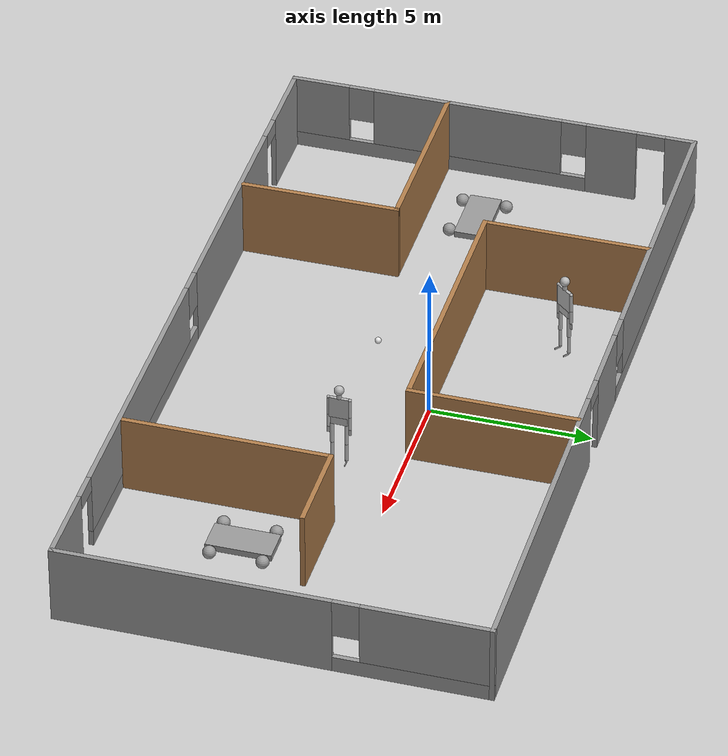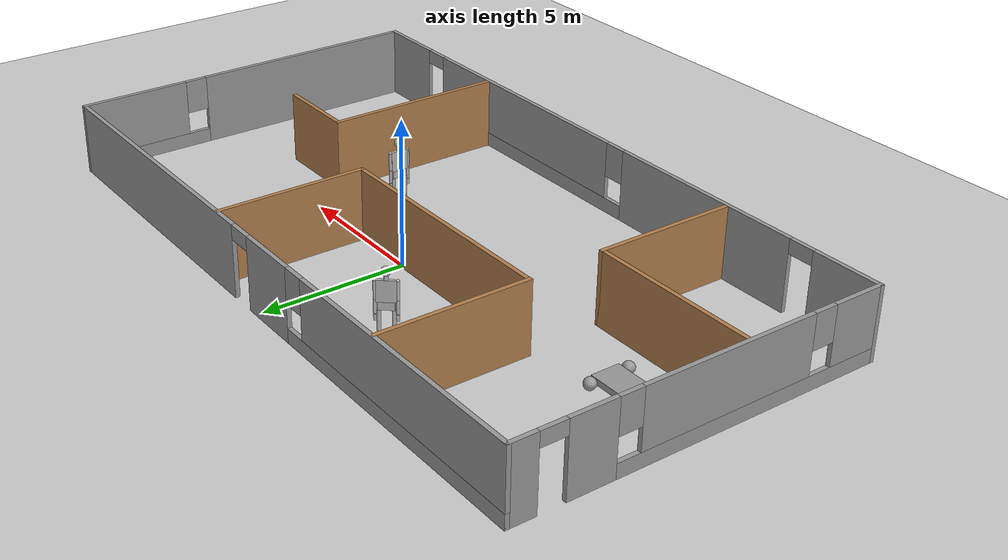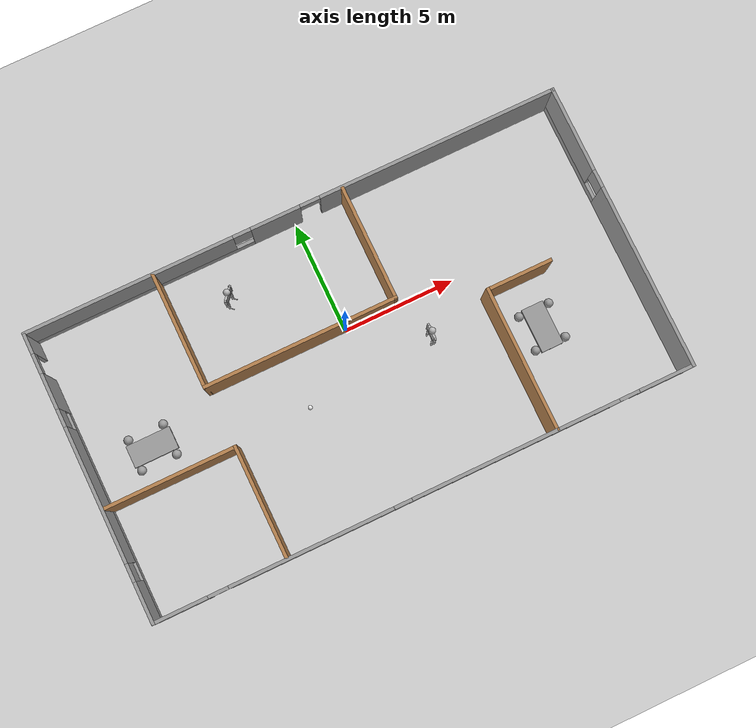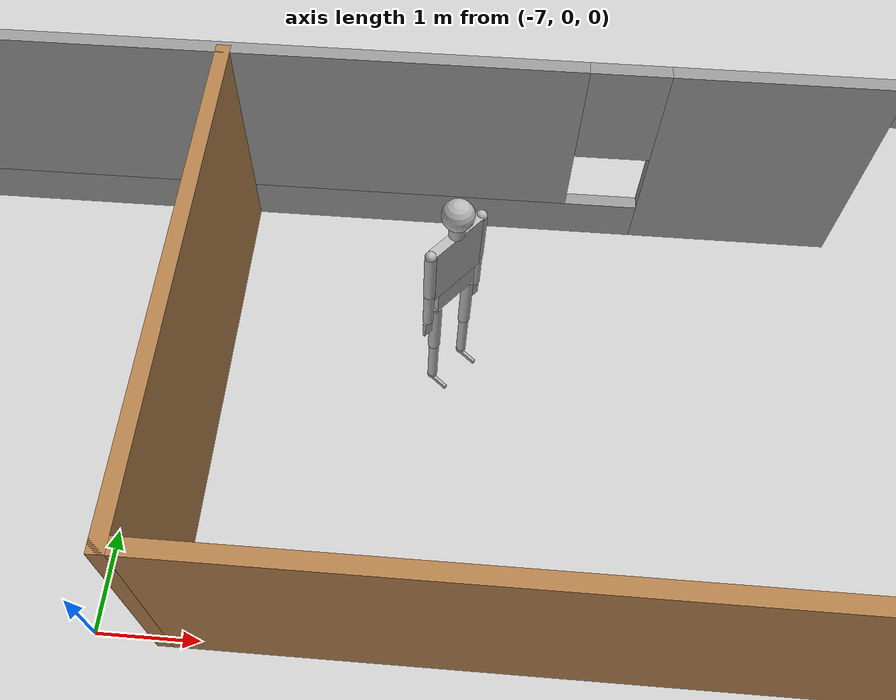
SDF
<sdf version="1.7">
 <world name="default">
  <plugin name="message" filename="libmessage.so"/>
  <light name="sun" type="directional">
   <pose>0 0 10 0 -0 0</pose>
   <diffuse>0.8 0.8 0.8 1</diffuse>
   <specular>0.2 0.2 0.2 1</specular>
   <attenuation>
    <range>1000</range>
    <constant>0.9</constant>
    <linear>0.01</linear>
    <quadratic>0.001</quadratic>
   </attenuation>
   <direction>-0.5 0.1 -0.9</direction>
   <spot><inner_angle>0</inner_angle><outer_angle>0</outer_angle><falloff>0</falloff></spot>
  </light>
  <model name="ground_plane">
   <static>1</static>
   <link name="link">
    <collision name="collision">
     <geometry><plane><normal>0 0 1</normal><size>100 100</size></plane></geometry>
     <surface>
      <contact><collide_bitmask>65535</collide_bitmask></contact>
      <friction><ode><mu>100</mu><mu2>50</mu2></ode></friction>
     </surface>
    </collision>
    <visual name="visual">
     <cast_shadows>0</cast_shadows>
     <geometry><plane><normal>0 0 1</normal><size>100 100</size></plane></geometry>
     <material>
      <script><uri>file://media/materials/scripts/gazebo.material</uri><name>Gazebo/Grey</name></script>
     </material>
    </visual>
   </link>
  </model>
  <gravity>0 0 -9.8</gravity>
  <magnetic_field>6e-06 2.3e-05 -4.2e-05</magnetic_field>
  <atmosphere type="adiabatic"/>
  <physics name="default_physics" default="0" type="ode">
   <max_step_size>0.001</max_step_size>
   <real_time_factor>1</real_time_factor>
   <real_time_update_rate>1000</real_time_update_rate>
  </physics>
  <scene><ambient>0.4 0.4 0.4 1</ambient><background>0.7 0.7 0.7 1</background><shadows>1</shadows></scene>
  <spherical_coordinates>
   <surface_model>EARTH_WGS84</surface_model>
   <latitude_deg>0</latitude_deg>
   <longitude_deg>0</longitude_deg>
   <elevation>0</elevation>
   <heading_deg>0</heading_deg>
  </spherical_coordinates>
  <model name="building">
   <pose>-0.0294 -1.27289 0 0 -0 0</pose>
   <link name="Wall_0">
    <pose>-12.05 0 0 0 0 -1.5708</pose>
    <visual name="Wall_0_Visual_0">
     <pose>-6.00515 0 1.25 0 -0 0</pose>
     <geometry><box><size>0.989706 0.15 2.5</size></box></geometry>
     <material>
      <script><uri>file://media/materials/scripts/gazebo.material</uri><name>Gazebo/Grey</name></script>
      <ambient>0.0823529 0.0823529 0.0823529 1</ambient>
     </material>
     <meta><layer>0</layer></meta>
    </visual>
    <collision name="Wall_0_Collision_0">
     <geometry><box><size>0.989706 0.15 2.5</size></box></geometry>
     <pose>-6.00515 0 1.25 0 -0 0</pose>
    </collision>
    <visual name="Wall_0_Visual_1">
     <pose>-3.80937 0 1.25 0 -0 0</pose>
     <geometry><box><size>1.60184 0.15 2.5</size></box></geometry>
     <material>
      <script><uri>file://media/materials/scripts/gazebo.material</uri><name>Gazebo/Grey</name></script>
      <ambient>0.0823529 0.0823529 0.0823529 1</ambient>
     </material>
     <meta><layer>0</layer></meta>
    </visual>
    <collision name="Wall_0_Collision_1">
     <geometry><box><size>1.60184 0.15 2.5</size></box></geometry>
     <pose>-3.80937 0 1.25 0 -0 0</pose>
    </collision>
    <visual name="Wall_0_Visual_2">
     <pose>1.74578 0 0.25 0 -0 0</pose>
     <geometry><box><size>9.50845 0.15 0.5</size></box></geometry>
     <material>
      <script><uri>file://media/materials/scripts/gazebo.material</uri><name>Gazebo/Grey</name></script>
      <ambient>0.0823529 0.0823529 0.0823529 1</ambient>
     </material>
     <meta><layer>0</layer></meta>
    </visual>
    <collision name="Wall_0_Collision_2">
     <geometry><box><size>9.50845 0.15 0.5</size></box></geometry>
     <pose>1.74578 0 0.25 0 -0 0</pose>
    </collision>
    <visual name="Wall_0_Visual_3">
     <pose>0.81488 0 1.5 0 -0 0</pose>
     <geometry><box><size>6.04666 0.15 2</size></box></geometry>
     <material>
      <script><uri>file://media/materials/scripts/gazebo.material</uri><name>Gazebo/Grey</name></script>
      <ambient>0.0823529 0.0823529 0.0823529 1</ambient>
     </material>
     <meta><layer>0</layer></meta>
    </visual>
    <collision name="Wall_0_Collision_3">
     <geometry><box><size>6.04666 0.15 2</size></box></geometry>
     <pose>0.81488 0 1.5 0 -0 0</pose>
    </collision>
    <visual name="Wall_0_Visual_4">
     <pose>5.56911 0 1.5 0 -0 0</pose>
     <geometry><box><size>1.86179 0.15 2</size></box></geometry>
     <material>
      <script><uri>file://media/materials/scripts/gazebo.material</uri><name>Gazebo/Grey</name></script>
      <ambient>0.0823529 0.0823529 0.0823529 1</ambient>
     </material>
     <meta><layer>0</layer></meta>
    </visual>
    <collision name="Wall_0_Collision_4">
     <geometry><box><size>1.86179 0.15 2</size></box></geometry>
     <pose>5.56911 0 1.5 0 -0 0</pose>
    </collision>
    <visual name="Wall_0_Visual_5">
     <pose>-2.60845 0 1.9 0 -0 0</pose>
     <geometry><box><size>0.8 0.15 1.2</size></box></geometry>
     <material>
      <script><uri>file://media/materials/scripts/gazebo.material</uri><name>Gazebo/Grey</name></script>
      <ambient>0.0823529 0.0823529 0.0823529 1</ambient>
     </material>
     <meta><layer>0</layer></meta>
    </visual>
    <collision name="Wall_0_Collision_5">
     <geometry><box><size>0.8 0.15 1.2</size></box></geometry>
     <pose>-2.60845 0 1.9 0 -0 0</pose>
    </collision>
    <visual name="Wall_0_Visual_6">
     <pose>4.23821 0 1.9 0 -0 0</pose>
     <geometry><box><size>0.8 0.15 1.2</size></box></geometry>
     <material>
      <script><uri>file://media/materials/scripts/gazebo.material</uri><name>Gazebo/Grey</name></script>
      <ambient>0.0823529 0.0823529 0.0823529 1</ambient>
     </material>
     <meta><layer>0</layer></meta>
    </visual>
    <collision name="Wall_0_Collision_6">
     <geometry><box><size>0.8 0.15 1.2</size></box></geometry>
     <pose>4.23821 0 1.9 0 -0 0</pose>
    </collision>
    <visual name="Wall_0_Visual_7">
     <pose>-5.06029 0 2.25 0 -0 0</pose>
     <geometry><box><size>0.9 0.15 0.5</size></box></geometry>
     <material>
      <script><uri>file://media/materials/scripts/gazebo.material</uri><name>Gazebo/Grey</name></script>
      <ambient>0.0823529 0.0823529 0.0823529 1</ambient>
     </material>
     <meta><layer>0</layer></meta>
    </visual>
    <collision name="Wall_0_Collision_7">
     <geometry><box><size>0.9 0.15 0.5</size></box></geometry>
     <pose>-5.06029 0 2.25 0 -0 0</pose>
    </collision>
   </link>
   <link name="Wall_1">
    <pose>0 -6.425 0 0 -0 0</pose>
    <visual name="Wall_1_Visual_0">
     <pose>-10.89 0 1.25 0 -0 0</pose>
     <geometry><box><size>2.47006 0.15 2.5</size></box></geometry>
     <material>
      <script><uri>file://media/materials/scripts/gazebo.material</uri><name>Gazebo/Grey</name></script>
      <ambient>0.0823529 0.0823529 0.0823529 1</ambient>
     </material>
     <meta><layer>0</layer></meta>
    </visual>
    <collision name="Wall_1_Collision_0">
     <geometry><box><size>2.47006 0.15 2.5</size></box></geometry>
     <pose>-10.89 0 1.25 0 -0 0</pose>
    </collision>
    <visual name="Wall_1_Visual_1">
     <pose>-5.09738 0 1.25 0 -0 0</pose>
     <geometry><box><size>7.3151 0.15 2.5</size></box></geometry>
     <material>
      <script><uri>file://media/materials/scripts/gazebo.material</uri><name>Gazebo/Grey</name></script>
      <ambient>0.0823529 0.0823529 0.0823529 1</ambient>
     </material>
     <meta><layer>0</layer></meta>
    </visual>
    <collision name="Wall_1_Collision_1">
     <geometry><box><size>7.3151 0.15 2.5</size></box></geometry>
     <pose>-5.09738 0 1.25 0 -0 0</pose>
    </collision>
    <visual name="Wall_1_Visual_2">
     <pose>10.8563 0 1.25 0 -0 0</pose>
     <geometry><box><size>2.53736 0.15 2.5</size></box></geometry>
     <material>
      <script><uri>file://media/materials/scripts/gazebo.material</uri><name>Gazebo/Grey</name></script>
      <ambient>0.0823529 0.0823529 0.0823529 1</ambient>
     </material>
     <meta><layer>0</layer></meta>
    </visual>
    <collision name="Wall_1_Collision_2">
     <geometry><box><size>2.53736 0.15 2.5</size></box></geometry>
     <pose>10.8563 0 1.25 0 -0 0</pose>
    </collision>
    <visual name="Wall_1_Visual_3">
     <pose>3.6239 0 0.25 0 -0 0</pose>
     <geometry><box><size>10.1275 0.15 0.5</size></box></geometry>
     <material>
      <script><uri>file://media/materials/scripts/gazebo.material</uri><name>Gazebo/Grey</name></script>
      <ambient>0.0823529 0.0823529 0.0823529 1</ambient>
     </material>
     <meta><layer>0</layer></meta>
    </visual>
    <collision name="Wall_1_Collision_3">
     <geometry><box><size>10.1275 0.15 0.5</size></box></geometry>
     <pose>3.6239 0 0.25 0 -0 0</pose>
    </collision>
    <visual name="Wall_1_Visual_4">
     <pose>4.0239 0 1.5 0 -0 0</pose>
     <geometry><box><size>9.32747 0.15 2</size></box></geometry>
     <material>
      <script><uri>file://media/materials/scripts/gazebo.material</uri><name>Gazebo/Grey</name></script>
      <ambient>0.0823529 0.0823529 0.0823529 1</ambient>
     </material>
     <meta><layer>0</layer></meta>
    </visual>
    <collision name="Wall_1_Collision_4">
     <geometry><box><size>9.32747 0.15 2</size></box></geometry>
     <pose>4.0239 0 1.5 0 -0 0</pose>
    </collision>
    <visual name="Wall_1_Visual_5">
     <pose>-1.03983 0 1.9 0 -0 0</pose>
     <geometry><box><size>0.8 0.15 1.2</size></box></geometry>
     <material>
      <script><uri>file://media/materials/scripts/gazebo.material</uri><name>Gazebo/Grey</name></script>
      <ambient>0.0823529 0.0823529 0.0823529 1</ambient>
     </material>
     <meta><layer>0</layer></meta>
    </visual>
    <collision name="Wall_1_Collision_5">
     <geometry><box><size>0.8 0.15 1.2</size></box></geometry>
     <pose>-1.03983 0 1.9 0 -0 0</pose>
    </collision>
    <visual name="Wall_1_Visual_6">
     <pose>-9.20494 0 2.25 0 -0 0</pose>
     <geometry><box><size>0.9 0.15 0.5</size></box></geometry>
     <material>
      <script><uri>file://media/materials/scripts/gazebo.material</uri><name>Gazebo/Grey</name></script>
      <ambient>0.0823529 0.0823529 0.0823529 1</ambient>
     </material>
     <meta><layer>0</layer></meta>
    </visual>
    <collision name="Wall_1_Collision_6">
     <geometry><box><size>0.9 0.15 0.5</size></box></geometry>
     <pose>-9.20494 0 2.25 0 -0 0</pose>
    </collision>
    <visual name="Wall_1_Visual_7">
     <pose>9.13764 0 2.25 0 -0 0</pose>
     <geometry><box><size>0.9 0.15 0.5</size></box></geometry>
     <material>
      <script><uri>file://media/materials/scripts/gazebo.material</uri><name>Gazebo/Grey</name></script>
      <ambient>0.0823529 0.0823529 0.0823529 1</ambient>
     </material>
     <meta><layer>0</layer></meta>
    </visual>
    <collision name="Wall_1_Collision_7">
     <geometry><box><size>0.9 0.15 0.5</size></box></geometry>
     <pose>9.13764 0 2.25 0 -0 0</pose>
    </collision>
   </link>
   <link name="Wall_10">
    <collision name="Wall_10_Collision">
     <geometry><box><size>3 0.15 2.5</size></box></geometry>
     <pose>0 0 1.25 0 -0 0</pose>
    </collision>
    <visual name="Wall_10_Visual">
     <pose>0 0 1.25 0 -0 0</pose>
     <geometry><box><size>3 0.15 2.5</size></box></geometry>
     <material>
      <script><uri>file://media/materials/scripts/gazebo.material</uri><name>Gazebo/Wood</name></script>
      <ambient>1 1 1 1</ambient>
     </material>
     <meta><layer>0</layer></meta>
    </visual>
    <pose>7.30122 -0.039357 0 0 -0 0</pose>
   </link>
   <link name="Wall_12">
    <collision name="Wall_12_Collision">
     <geometry><box><size>6 0.15 2.5</size></box></geometry>
     <pose>0 0 1.25 0 -0 0</pose>
    </collision>
    <visual name="Wall_12_Visual">
     <pose>0 0 1.25 0 -0 0</pose>
     <geometry><box><size>6 0.15 2.5</size></box></geometry>
     <material>
      <script><uri>file://media/materials/scripts/gazebo.material</uri><name>Gazebo/Wood</name></script>
      <ambient>1 1 1 1</ambient>
     </material>
     <meta><layer>0</layer></meta>
    </visual>
    <pose>-9.10187 -1.46254 0 0 -0 0</pose>
   </link>
   <link name="Wall_13">
    <collision name="Wall_13_Collision">
     <geometry><box><size>5 0.15 2.5</size></box></geometry>
     <pose>0 0 1.25 0 -0 0</pose>
    </collision>
    <visual name="Wall_13_Visual">
     <pose>0 0 1.25 0 -0 0</pose>
     <geometry><box><size>5 0.15 2.5</size></box></geometry>
     <material>
      <script><uri>file://media/materials/scripts/gazebo.material</uri><name>Gazebo/Wood</name></script>
      <ambient>1 1 1 1</ambient>
     </material>
     <meta><layer>0</layer></meta>
    </visual>
    <pose>-6.17687 -3.88754 0 0 0 -1.5708</pose>
   </link>
   <link name="Wall_2">
    <pose>12.05 0 0 0 -0 1.5708</pose>
    <visual name="Wall_2_Visual_0">
     <pose>-2.35395 0 1.25 0 -0 0</pose>
     <geometry><box><size>8.2921 0.15 2.5</size></box></geometry>
     <material>
      <script><uri>file://media/materials/scripts/gazebo.material</uri><name>Gazebo/Grey</name></script>
      <ambient>0.0823529 0.0823529 0.0823529 1</ambient>
     </material>
     <meta><layer>0</layer></meta>
    </visual>
    <collision name="Wall_2_Collision_0">
     <geometry><box><size>8.2921 0.15 2.5</size></box></geometry>
     <pose>-2.35395 0 1.25 0 -0 0</pose>
    </collision>
    <visual name="Wall_2_Visual_1">
     <pose>4.14605 0 0.25 0 -0 0</pose>
     <geometry><box><size>4.7079 0.15 0.5</size></box></geometry>
     <material>
      <script><uri>file://media/materials/scripts/gazebo.material</uri><name>Gazebo/Grey</name></script>
      <ambient>0.0823529 0.0823529 0.0823529 1</ambient>
     </material>
     <meta><layer>0</layer></meta>
    </visual>
    <collision name="Wall_2_Collision_1">
     <geometry><box><size>4.7079 0.15 0.5</size></box></geometry>
     <pose>4.14605 0 0.25 0 -0 0</pose>
    </collision>
    <visual name="Wall_2_Visual_2">
     <pose>4.54605 0 1.5 0 -0 0</pose>
     <geometry><box><size>3.9079 0.15 2</size></box></geometry>
     <material>
      <script><uri>file://media/materials/scripts/gazebo.material</uri><name>Gazebo/Grey</name></script>
      <ambient>0.0823529 0.0823529 0.0823529 1</ambient>
     </material>
     <meta><layer>0</layer></meta>
    </visual>
    <collision name="Wall_2_Collision_2">
     <geometry><box><size>3.9079 0.15 2</size></box></geometry>
     <pose>4.54605 0 1.5 0 -0 0</pose>
    </collision>
    <visual name="Wall_2_Visual_3">
     <pose>2.1921 0 1.9 0 -0 0</pose>
     <geometry><box><size>0.8 0.15 1.2</size></box></geometry>
     <material>
      <script><uri>file://media/materials/scripts/gazebo.material</uri><name>Gazebo/Grey</name></script>
      <ambient>0.0823529 0.0823529 0.0823529 1</ambient>
     </material>
     <meta><layer>0</layer></meta>
    </visual>
    <collision name="Wall_2_Collision_3">
     <geometry><box><size>0.8 0.15 1.2</size></box></geometry>
     <pose>2.1921 0 1.9 0 -0 0</pose>
    </collision>
   </link>
   <link name="Wall_3">
    <pose>0 6.425 0 0 -0 3.14159</pose>
    <visual name="Wall_3_Visual_0">
     <pose>-6.70437 0 1.25 0 -0 0</pose>
     <geometry><box><size>10.8413 0.15 2.5</size></box></geometry>
     <material>
      <script><uri>file://media/materials/scripts/gazebo.material</uri><name>Gazebo/Grey</name></script>
      <ambient>0.0823529 0.0823529 0.0823529 1</ambient>
     </material>
     <meta><layer>0</layer></meta>
    </visual>
    <collision name="Wall_3_Collision_0">
     <geometry><box><size>10.8413 0.15 2.5</size></box></geometry>
     <pose>-6.70437 0 1.25 0 -0 0</pose>
    </collision>
    <visual name="Wall_3_Visual_1">
     <pose>0.741002 0 1.25 0 -0 0</pose>
     <geometry><box><size>2.2495 0.15 2.5</size></box></geometry>
     <material>
      <script><uri>file://media/materials/scripts/gazebo.material</uri><name>Gazebo/Grey</name></script>
      <ambient>0.0823529 0.0823529 0.0823529 1</ambient>
     </material>
     <meta><layer>0</layer></meta>
    </visual>
    <collision name="Wall_3_Collision_1">
     <geometry><box><size>2.2495 0.15 2.5</size></box></geometry>
     <pose>0.741002 0 1.25 0 -0 0</pose>
    </collision>
    <visual name="Wall_3_Visual_2">
     <pose>6.99538 0 0.25 0 -0 0</pose>
     <geometry><box><size>10.2592 0.15 0.5</size></box></geometry>
     <material>
      <script><uri>file://media/materials/scripts/gazebo.material</uri><name>Gazebo/Grey</name></script>
      <ambient>0.0823529 0.0823529 0.0823529 1</ambient>
     </material>
     <meta><layer>0</layer></meta>
    </visual>
    <collision name="Wall_3_Collision_2">
     <geometry><box><size>10.2592 0.15 0.5</size></box></geometry>
     <pose>6.99538 0 0.25 0 -0 0</pose>
    </collision>
    <visual name="Wall_3_Visual_3">
     <pose>7.39538 0 1.5 0 -0 0</pose>
     <geometry><box><size>9.45925 0.15 2</size></box></geometry>
     <material>
      <script><uri>file://media/materials/scripts/gazebo.material</uri><name>Gazebo/Grey</name></script>
      <ambient>0.0823529 0.0823529 0.0823529 1</ambient>
     </material>
     <meta><layer>0</layer></meta>
    </visual>
    <collision name="Wall_3_Collision_3">
     <geometry><box><size>9.45925 0.15 2</size></box></geometry>
     <pose>7.39538 0 1.5 0 -0 0</pose>
    </collision>
    <visual name="Wall_3_Visual_4">
     <pose>2.26575 0 1.9 0 -0 0</pose>
     <geometry><box><size>0.8 0.15 1.2</size></box></geometry>
     <material>
      <script><uri>file://media/materials/scripts/gazebo.material</uri><name>Gazebo/Grey</name></script>
      <ambient>0.0823529 0.0823529 0.0823529 1</ambient>
     </material>
     <meta><layer>0</layer></meta>
    </visual>
    <collision name="Wall_3_Collision_4">
     <geometry><box><size>0.8 0.15 1.2</size></box></geometry>
     <pose>2.26575 0 1.9 0 -0 0</pose>
    </collision>
    <visual name="Wall_3_Visual_5">
     <pose>-0.833748 0 2.25 0 -0 0</pose>
     <geometry><box><size>0.9 0.15 0.5</size></box></geometry>
     <material>
      <script><uri>file://media/materials/scripts/gazebo.material</uri><name>Gazebo/Grey</name></script>
      <ambient>0.0823529 0.0823529 0.0823529 1</ambient>
     </material>
     <meta><layer>0</layer></meta>
    </visual>
    <collision name="Wall_3_Collision_5">
     <geometry><box><size>0.9 0.15 0.5</size></box></geometry>
     <pose>-0.833748 0 2.25 0 -0 0</pose>
    </collision>
   </link>
   <link name="Wall_5">
    <collision name="Wall_5_Collision">
     <geometry><box><size>5.25 0.15 2.5</size></box></geometry>
     <pose>0 0 1.25 0 -0 0</pose>
    </collision>
    <visual name="Wall_5_Visual">
     <pose>0 0 1.25 0 -0 0</pose>
     <geometry><box><size>5.25 0.15 2.5</size></box></geometry>
     <material>
      <script><uri>file://media/materials/scripts/gazebo.material</uri><name>Gazebo/Wood</name></script>
      <ambient>1 1 1 1</ambient>
     </material>
     <meta><layer>0</layer></meta>
    </visual>
    <pose>-6.29048 3.82874 0 0 0 -1.5708</pose>
   </link>
   <link name="Wall_6">
    <collision name="Wall_6_Collision">
     <geometry><box><size>8.75 0.15 2.5</size></box></geometry>
     <pose>0 0 1.25 0 -0 0</pose>
    </collision>
    <visual name="Wall_6_Visual">
     <pose>0 0 1.25 0 -0 0</pose>
     <geometry><box><size>8.75 0.15 2.5</size></box></geometry>
     <material>
      <script><uri>file://media/materials/scripts/gazebo.material</uri><name>Gazebo/Wood</name></script>
      <ambient>1 1 1 1</ambient>
     </material>
     <meta><layer>0</layer></meta>
    </visual>
    <pose>-1.99048 1.27874 0 0 -0 0</pose>
   </link>
   <link name="Wall_7">
    <collision name="Wall_7_Collision">
     <geometry><box><size>5.25 0.15 2.5</size></box></geometry>
     <pose>0 0 1.25 0 -0 0</pose>
    </collision>
    <visual name="Wall_7_Visual">
     <pose>0 0 1.25 0 -0 0</pose>
     <geometry><box><size>5.25 0.15 2.5</size></box></geometry>
     <material>
      <script><uri>file://media/materials/scripts/gazebo.material</uri><name>Gazebo/Wood</name></script>
      <ambient>1 1 1 1</ambient>
     </material>
     <meta><layer>0</layer></meta>
    </visual>
    <pose>2.30952 3.82874 0 0 -0 1.5708</pose>
   </link>
   <link name="Wall_9">
    <collision name="Wall_9_Collision">
     <geometry><box><size>6.5 0.15 2.5</size></box></geometry>
     <pose>0 0 1.25 0 -0 0</pose>
    </collision>
    <visual name="Wall_9_Visual">
     <pose>0 0 1.25 0 -0 0</pose>
     <geometry><box><size>6.5 0.15 2.5</size></box></geometry>
     <material>
      <script><uri>file://media/materials/scripts/gazebo.material</uri><name>Gazebo/Wood</name></script>
      <ambient>1 1 1 1</ambient>
     </material>
     <meta><layer>0</layer></meta>
    </visual>
    <pose>5.87622 -3.21436 0 0 -0 1.5708</pose>
   </link>
   <static>1</static>
  </model>
  <model name="object">
   <link name="link_0">
    <pose>-2.35749 -2.62116 0.5 0 -0 0</pose>
    <inertial>
     <mass>1</mass>
     <inertia>
      <ixx>0.166667</ixx>
      <ixy>0</ixy>
      <ixz>0</ixz>
      <iyy>0.166667</iyy>
      <iyz>0</iyz>
      <izz>0.166667</izz>
     </inertia>
    </inertial>
    <visual name="visual">
     <geometry><box><size>2 1 0.2</size></box></geometry>
     <material>
      <lighting>1</lighting>
      <script><uri>file://media/materials/scripts/gazebo.material</uri><name>Gazebo/Grey</name></script>
      <shader type="pixel"><normal_map>__default__</normal_map></shader>
      <ambient>0.3 0.3 0.3 1</ambient>
      <diffuse>0.7 0.7 0.7 1</diffuse>
      <specular>0.01 0.01 0.01 1</specular>
      <emissive>0 0 0 1</emissive>
     </material>
    </visual>
    <collision name="collision">
     <geometry><box><size>2 1 0.2</size></box></geometry>
     <surface>
      <friction>
       <ode><mu>1</mu><mu2>1</mu2><fdir1>0 0 0</fdir1><slip1>0</slip1><slip2>0</slip2></ode>
       <torsional>
        <coefficient>1</coefficient>
        <patch_radius>0</patch_radius>
        <surface_radius>0</surface_radius>
        <use_patch_radius>1</use_patch_radius>
        <ode><slip>0</slip></ode>
       </torsional>
      </friction>
      <bounce><restitution_coefficient>0</restitution_coefficient><threshold>1e+06</threshold></bounce>
      <contact>
       <collide_without_contact>0</collide_without_contact>
       <collide_without_contact_bitmask>1</collide_without_contact_bitmask>
       <collide_bitmask>1</collide_bitmask>
       <ode>
        <soft_cfm>0</soft_cfm>
        <soft_erp>0.2</soft_erp>
        <kp>1e+13</kp>
        <kd>1</kd>
        <max_vel>0.01</max_vel>
        <min_depth>0</min_depth>
       </ode>
       <bullet>
        <split_impulse>1</split_impulse>
        <split_impulse_penetration_threshold>-0.01</split_impulse_penetration_threshold>
        <soft_cfm>0</soft_cfm>
        <soft_erp>0.2</soft_erp>
        <kp>1e+13</kp>
        <kd>1</kd>
       </bullet>
      </contact>
     </surface>
    </collision>
   </link>
   <link name="link_3">
    <pose>-3.15749 -3.32116 0.5 0 -0 0</pose>
    <inertial>
     <mass>1</mass>
     <inertia><ixx>0.1</ixx><ixy>0</ixy><ixz>0</ixz><iyy>0.1</iyy><iyz>0</iyz><izz>0.1</izz></inertia>
    </inertial>
    <visual name="visual">
     <geometry><sphere><radius>0.2</radius></sphere></geometry>
     <material>
      <lighting>1</lighting>
      <script><uri>file://media/materials/scripts/gazebo.material</uri><name>Gazebo/Grey</name></script>
      <shader type="pixel"><normal_map>__default__</normal_map></shader>
      <ambient>0.3 0.3 0.3 1</ambient>
      <diffuse>0.7 0.7 0.7 1</diffuse>
      <specular>0.01 0.01 0.01 1</specular>
      <emissive>0 0 0 1</emissive>
     </material>
    </visual>
    <collision name="collision">
     <geometry><sphere><radius>0.2</radius></sphere></geometry>
     <surface>
      <friction>
       <ode><mu>1</mu><mu2>1</mu2><fdir1>0 0 0</fdir1><slip1>0</slip1><slip2>0</slip2></ode>
       <torsional>
        <coefficient>1</coefficient>
        <patch_radius>0</patch_radius>
        <surface_radius>0</surface_radius>
        <use_patch_radius>1</use_patch_radius>
        <ode><slip>0</slip></ode>
       </torsional>
      </friction>
      <bounce><restitution_coefficient>0</restitution_coefficient><threshold>1e+06</threshold></bounce>
      <contact>
       <collide_without_contact>0</collide_without_contact>
       <collide_without_contact_bitmask>1</collide_without_contact_bitmask>
       <collide_bitmask>1</collide_bitmask>
       <ode>
        <soft_cfm>0</soft_cfm>
        <soft_erp>0.2</soft_erp>
        <kp>1e+13</kp>
        <kd>1</kd>
        <max_vel>0.01</max_vel>
        <min_depth>0</min_depth>
       </ode>
       <bullet>
        <split_impulse>1</split_impulse>
        <split_impulse_penetration_threshold>-0.01</split_impulse_penetration_threshold>
        <soft_cfm>0</soft_cfm>
        <soft_erp>0.2</soft_erp>
        <kp>1e+13</kp>
        <kd>1</kd>
       </bullet>
      </contact>
     </surface>
    </collision>
   </link>
   <link name="link_3_clone">
    <pose>-3.15749 -1.92116 0.5 0 -0 0</pose>
    <inertial>
     <mass>1</mass>
     <inertia><ixx>0.1</ixx><ixy>0</ixy><ixz>0</ixz><iyy>0.1</iyy><iyz>0</iyz><izz>0.1</izz></inertia>
    </inertial>
    <visual name="visual">
     <geometry><sphere><radius>0.2</radius></sphere></geometry>
     <material>
      <lighting>1</lighting>
      <script><uri>file://media/materials/scripts/gazebo.material</uri><name>Gazebo/Grey</name></script>
      <shader type="pixel"><normal_map>__default__</normal_map></shader>
      <ambient>0.3 0.3 0.3 1</ambient>
      <diffuse>0.7 0.7 0.7 1</diffuse>
      <specular>0.01 0.01 0.01 1</specular>
      <emissive>0 0 0 1</emissive>
     </material>
    </visual>
    <collision name="collision">
     <geometry><sphere><radius>0.2</radius></sphere></geometry>
     <surface>
      <friction>
       <ode><mu>1</mu><mu2>1</mu2><fdir1>0 0 0</fdir1><slip1>0</slip1><slip2>0</slip2></ode>
       <torsional>
        <coefficient>1</coefficient>
        <patch_radius>0</patch_radius>
        <surface_radius>0</surface_radius>
        <use_patch_radius>1</use_patch_radius>
        <ode><slip>0</slip></ode>
       </torsional>
      </friction>
      <bounce><restitution_coefficient>0</restitution_coefficient><threshold>1e+06</threshold></bounce>
      <contact>
       <collide_without_contact>0</collide_without_contact>
       <collide_without_contact_bitmask>1</collide_without_contact_bitmask>
       <collide_bitmask>1</collide_bitmask>
       <ode>
        <soft_cfm>0</soft_cfm>
        <soft_erp>0.2</soft_erp>
        <kp>1e+13</kp>
        <kd>1</kd>
        <max_vel>0.01</max_vel>
        <min_depth>0</min_depth>
       </ode>
       <bullet>
        <split_impulse>1</split_impulse>
        <split_impulse_penetration_threshold>-0.01</split_impulse_penetration_threshold>
        <soft_cfm>0</soft_cfm>
        <soft_erp>0.2</soft_erp>
        <kp>1e+13</kp>
        <kd>1</kd>
       </bullet>
      </contact>
     </surface>
    </collision>
   </link>
   <link name="link_3_clone_0">
    <pose>-1.55749 -3.32116 0.5 0 -0 0</pose>
    <inertial>
     <mass>1</mass>
     <inertia><ixx>0.1</ixx><ixy>0</ixy><ixz>0</ixz><iyy>0.1</iyy><iyz>0</iyz><izz>0.1</izz></inertia>
    </inertial>
    <visual name="visual">
     <geometry><sphere><radius>0.2</radius></sphere></geometry>
     <material>
      <lighting>1</lighting>
      <script><uri>file://media/materials/scripts/gazebo.material</uri><name>Gazebo/Grey</name></script>
      <shader type="pixel"><normal_map>__default__</normal_map></shader>
      <ambient>0.3 0.3 0.3 1</ambient>
      <diffuse>0.7 0.7 0.7 1</diffuse>
      <specular>0.01 0.01 0.01 1</specular>
      <emissive>0 0 0 1</emissive>
     </material>
    </visual>
    <collision name="collision">
     <geometry><sphere><radius>0.2</radius></sphere></geometry>
     <surface>
      <friction>
       <ode><mu>1</mu><mu2>1</mu2><fdir1>0 0 0</fdir1><slip1>0</slip1><slip2>0</slip2></ode>
       <torsional>
        <coefficient>1</coefficient>
        <patch_radius>0</patch_radius>
        <surface_radius>0</surface_radius>
        <use_patch_radius>1</use_patch_radius>
        <ode><slip>0</slip></ode>
       </torsional>
      </friction>
      <bounce><restitution_coefficient>0</restitution_coefficient><threshold>1e+06</threshold></bounce>
      <contact>
       <collide_without_contact>0</collide_without_contact>
       <collide_without_contact_bitmask>1</collide_without_contact_bitmask>
       <collide_bitmask>1</collide_bitmask>
       <ode>
        <soft_cfm>0</soft_cfm>
        <soft_erp>0.2</soft_erp>
        <kp>1e+13</kp>
        <kd>1</kd>
        <max_vel>0.01</max_vel>
        <min_depth>0</min_depth>
       </ode>
       <bullet>
        <split_impulse>1</split_impulse>
        <split_impulse_penetration_threshold>-0.01</split_impulse_penetration_threshold>
        <soft_cfm>0</soft_cfm>
        <soft_erp>0.2</soft_erp>
        <kp>1e+13</kp>
        <kd>1</kd>
       </bullet>
      </contact>
     </surface>
    </collision>
   </link>
   <link name="link_3_clone_1">
    <pose>-1.55749 -1.92116 0.5 0 -0 0</pose>
    <inertial>
     <mass>1</mass>
     <inertia><ixx>0.1</ixx><ixy>0</ixy><ixz>0</ixz><iyy>0.1</iyy><iyz>0</iyz><izz>0.1</izz></inertia>
    </inertial>
    <visual name="visual">
     <geometry><sphere><radius>0.2</radius></sphere></geometry>
     <material>
      <lighting>1</lighting>
      <script><uri>file://media/materials/scripts/gazebo.material</uri><name>Gazebo/Grey</name></script>
      <shader type="pixel"><normal_map>__default__</normal_map></shader>
      <ambient>0.3 0.3 0.3 1</ambient>
      <diffuse>0.7 0.7 0.7 1</diffuse>
      <specular>0.01 0.01 0.01 1</specular>
      <emissive>0 0 0 1</emissive>
     </material>
    </visual>
    <collision name="collision">
     <geometry><sphere><radius>0.2</radius></sphere></geometry>
     <surface>
      <friction>
       <ode><mu>1</mu><mu2>1</mu2><fdir1>0 0 0</fdir1><slip1>0</slip1><slip2>0</slip2></ode>
       <torsional>
        <coefficient>1</coefficient>
        <patch_radius>0</patch_radius>
        <surface_radius>0</surface_radius>
        <use_patch_radius>1</use_patch_radius>
        <ode><slip>0</slip></ode>
       </torsional>
      </friction>
      <bounce><restitution_coefficient>0</restitution_coefficient><threshold>1e+06</threshold></bounce>
      <contact>
       <collide_without_contact>0</collide_without_contact>
       <collide_without_contact_bitmask>1</collide_without_contact_bitmask>
       <collide_bitmask>1</collide_bitmask>
       <ode>
        <soft_cfm>0</soft_cfm>
        <soft_erp>0.2</soft_erp>
        <kp>1e+13</kp>
        <kd>1</kd>
        <max_vel>0.01</max_vel>
        <min_depth>0</min_depth>
       </ode>
       <bullet>
        <split_impulse>1</split_impulse>
        <split_impulse_penetration_threshold>-0.01</split_impulse_penetration_threshold>
        <soft_cfm>0</soft_cfm>
        <soft_erp>0.2</soft_erp>
        <kp>1e+13</kp>
        <kd>1</kd>
       </bullet>
      </contact>
     </surface>
    </collision>
   </link>
   <joint name="link_0_JOINT_0" type="revolute">
    <parent>link_0</parent>
    <child>link_3</child>
    <axis>
     <xyz>0 0 1</xyz>
     <limit>
      <lower>-1.79769e+308</lower>
      <upper>1.79769e+308</upper>
      <effort>-1</effort>
      <velocity>-1</velocity>
     </limit>
     <dynamics>
      <spring_reference>0</spring_reference>
      <spring_stiffness>0</spring_stiffness>
      <damping>0</damping>
     </dynamics>
    </axis>
    <physics>
     <ode><limit><cfm>0</cfm><erp>0.2</erp></limit><suspension><cfm>0</cfm><erp>0.2</erp></suspension></ode>
    </physics>
   </joint>
   <joint name="link_0_JOINT_1" type="revolute">
    <parent>link_0</parent>
    <child>link_3_clone</child>
    <axis>
     <xyz>0 0 1</xyz>
     <limit>
      <lower>-1.79769e+308</lower>
      <upper>1.79769e+308</upper>
      <effort>-1</effort>
      <velocity>-1</velocity>
     </limit>
     <dynamics>
      <spring_reference>0</spring_reference>
      <spring_stiffness>0</spring_stiffness>
      <damping>0</damping>
     </dynamics>
    </axis>
    <physics>
     <ode><limit><cfm>0</cfm><erp>0.2</erp></limit><suspension><cfm>0</cfm><erp>0.2</erp></suspension></ode>
    </physics>
   </joint>
   <joint name="link_0_JOINT_2" type="revolute">
    <parent>link_0</parent>
    <child>link_3_clone_0</child>
    <axis>
     <xyz>0 0 1</xyz>
     <limit>
      <lower>-1.79769e+308</lower>
      <upper>1.79769e+308</upper>
      <effort>-1</effort>
      <velocity>-1</velocity>
     </limit>
     <dynamics>
      <spring_reference>0</spring_reference>
      <spring_stiffness>0</spring_stiffness>
      <damping>0</damping>
     </dynamics>
    </axis>
    <physics>
     <ode><limit><cfm>0</cfm><erp>0.2</erp></limit><suspension><cfm>0</cfm><erp>0.2</erp></suspension></ode>
    </physics>
   </joint>
   <joint name="link_0_JOINT_3" type="revolute">
    <parent>link_0</parent>
    <child>link_3_clone_1</child>
    <axis>
     <xyz>0 0 1</xyz>
     <limit>
      <lower>-1.79769e+308</lower>
      <upper>1.79769e+308</upper>
      <effort>-1</effort>
      <velocity>-1</velocity>
     </limit>
     <dynamics>
      <spring_reference>0</spring_reference>
      <spring_stiffness>0</spring_stiffness>
      <damping>0</damping>
     </dynamics>
    </axis>
    <physics>
     <ode><limit><cfm>0</cfm><erp>0.2</erp></limit><suspension><cfm>0</cfm><erp>0.2</erp></suspension></ode>
    </physics>
   </joint>
   <static>0</static>
   <pose>-7.11702 1.59106 -0.300013 0 4e-06 0.002621</pose>
  </model>
  <model name="object_0">
   <link name="link_0">
    <pose>-2.35749 -2.62116 0.5 0 -0 0</pose>
    <inertial>
     <mass>1</mass>
     <inertia>
      <ixx>0.166667</ixx>
      <ixy>0</ixy>
      <ixz>0</ixz>
      <iyy>0.166667</iyy>
      <iyz>0</iyz>
      <izz>0.166667</izz>
     </inertia>
    </inertial>
    <visual name="visual">
     <geometry><box><size>2 1 0.2</size></box></geometry>
     <material>
      <lighting>1</lighting>
      <script><uri>file://media/materials/scripts/gazebo.material</uri><name>Gazebo/Grey</name></script>
      <shader type="pixel"><normal_map>__default__</normal_map></shader>
      <ambient>0.3 0.3 0.3 1</ambient>
      <diffuse>0.7 0.7 0.7 1</diffuse>
      <specular>0.01 0.01 0.01 1</specular>
      <emissive>0 0 0 1</emissive>
     </material>
    </visual>
    <collision name="collision">
     <geometry><box><size>2 1 0.2</size></box></geometry>
     <surface>
      <friction>
       <ode><mu>1</mu><mu2>1</mu2><fdir1>0 0 0</fdir1><slip1>0</slip1><slip2>0</slip2></ode>
       <torsional>
        <coefficient>1</coefficient>
        <patch_radius>0</patch_radius>
        <surface_radius>0</surface_radius>
        <use_patch_radius>1</use_patch_radius>
        <ode><slip>0</slip></ode>
       </torsional>
      </friction>
      <bounce><restitution_coefficient>0</restitution_coefficient><threshold>1e+06</threshold></bounce>
      <contact>
       <collide_without_contact>0</collide_without_contact>
       <collide_without_contact_bitmask>1</collide_without_contact_bitmask>
       <collide_bitmask>1</collide_bitmask>
       <ode>
        <soft_cfm>0</soft_cfm>
        <soft_erp>0.2</soft_erp>
        <kp>1e+13</kp>
        <kd>1</kd>
        <max_vel>0.01</max_vel>
        <min_depth>0</min_depth>
       </ode>
       <bullet>
        <split_impulse>1</split_impulse>
        <split_impulse_penetration_threshold>-0.01</split_impulse_penetration_threshold>
        <soft_cfm>0</soft_cfm>
        <soft_erp>0.2</soft_erp>
        <kp>1e+13</kp>
        <kd>1</kd>
       </bullet>
      </contact>
     </surface>
    </collision>
   </link>
   <link name="link_3">
    <pose>-3.15749 -3.32116 0.5 0 -0 0</pose>
    <inertial>
     <mass>1</mass>
     <inertia><ixx>0.1</ixx><ixy>0</ixy><ixz>0</ixz><iyy>0.1</iyy><iyz>0</iyz><izz>0.1</izz></inertia>
    </inertial>
    <visual name="visual">
     <geometry><sphere><radius>0.2</radius></sphere></geometry>
     <material>
      <lighting>1</lighting>
      <script><uri>file://media/materials/scripts/gazebo.material</uri><name>Gazebo/Grey</name></script>
      <shader type="pixel"><normal_map>__default__</normal_map></shader>
      <ambient>0.3 0.3 0.3 1</ambient>
      <diffuse>0.7 0.7 0.7 1</diffuse>
      <specular>0.01 0.01 0.01 1</specular>
      <emissive>0 0 0 1</emissive>
     </material>
    </visual>
    <collision name="collision">
     <geometry><sphere><radius>0.2</radius></sphere></geometry>
     <surface>
      <friction>
       <ode><mu>1</mu><mu2>1</mu2><fdir1>0 0 0</fdir1><slip1>0</slip1><slip2>0</slip2></ode>
       <torsional>
        <coefficient>1</coefficient>
        <patch_radius>0</patch_radius>
        <surface_radius>0</surface_radius>
        <use_patch_radius>1</use_patch_radius>
        <ode><slip>0</slip></ode>
       </torsional>
      </friction>
      <bounce><restitution_coefficient>0</restitution_coefficient><threshold>1e+06</threshold></bounce>
      <contact>
       <collide_without_contact>0</collide_without_contact>
       <collide_without_contact_bitmask>1</collide_without_contact_bitmask>
       <collide_bitmask>1</collide_bitmask>
       <ode>
        <soft_cfm>0</soft_cfm>
        <soft_erp>0.2</soft_erp>
        <kp>1e+13</kp>
        <kd>1</kd>
        <max_vel>0.01</max_vel>
        <min_depth>0</min_depth>
       </ode>
       <bullet>
        <split_impulse>1</split_impulse>
        <split_impulse_penetration_threshold>-0.01</split_impulse_penetration_threshold>
        <soft_cfm>0</soft_cfm>
        <soft_erp>0.2</soft_erp>
        <kp>1e+13</kp>
        <kd>1</kd>
       </bullet>
      </contact>
     </surface>
    </collision>
   </link>
   <link name="link_3_clone">
    <pose>-3.15749 -1.92116 0.5 0 -0 0</pose>
    <inertial>
     <mass>1</mass>
     <inertia><ixx>0.1</ixx><ixy>0</ixy><ixz>0</ixz><iyy>0.1</iyy><iyz>0</iyz><izz>0.1</izz></inertia>
    </inertial>
    <visual name="visual">
     <geometry><sphere><radius>0.2</radius></sphere></geometry>
     <material>
      <lighting>1</lighting>
      <script><uri>file://media/materials/scripts/gazebo.material</uri><name>Gazebo/Grey</name></script>
      <shader type="pixel"><normal_map>__default__</normal_map></shader>
      <ambient>0.3 0.3 0.3 1</ambient>
      <diffuse>0.7 0.7 0.7 1</diffuse>
      <specular>0.01 0.01 0.01 1</specular>
      <emissive>0 0 0 1</emissive>
     </material>
    </visual>
    <collision name="collision">
     <geometry><sphere><radius>0.2</radius></sphere></geometry>
     <surface>
      <friction>
       <ode><mu>1</mu><mu2>1</mu2><fdir1>0 0 0</fdir1><slip1>0</slip1><slip2>0</slip2></ode>
       <torsional>
        <coefficient>1</coefficient>
        <patch_radius>0</patch_radius>
        <surface_radius>0</surface_radius>
        <use_patch_radius>1</use_patch_radius>
        <ode><slip>0</slip></ode>
       </torsional>
      </friction>
      <bounce><restitution_coefficient>0</restitution_coefficient><threshold>1e+06</threshold></bounce>
      <contact>
       <collide_without_contact>0</collide_without_contact>
       <collide_without_contact_bitmask>1</collide_without_contact_bitmask>
       <collide_bitmask>1</collide_bitmask>
       <ode>
        <soft_cfm>0</soft_cfm>
        <soft_erp>0.2</soft_erp>
        <kp>1e+13</kp>
        <kd>1</kd>
        <max_vel>0.01</max_vel>
        <min_depth>0</min_depth>
       </ode>
       <bullet>
        <split_impulse>1</split_impulse>
        <split_impulse_penetration_threshold>-0.01</split_impulse_penetration_threshold>
        <soft_cfm>0</soft_cfm>
        <soft_erp>0.2</soft_erp>
        <kp>1e+13</kp>
        <kd>1</kd>
       </bullet>
      </contact>
     </surface>
    </collision>
   </link>
   <link name="link_3_clone_0">
    <pose>-1.55749 -3.32116 0.5 0 -0 0</pose>
    <inertial>
     <mass>1</mass>
     <inertia><ixx>0.1</ixx><ixy>0</ixy><ixz>0</ixz><iyy>0.1</iyy><iyz>0</iyz><izz>0.1</izz></inertia>
    </inertial>
    <visual name="visual">
     <geometry><sphere><radius>0.2</radius></sphere></geometry>
     <material>
      <lighting>1</lighting>
      <script><uri>file://media/materials/scripts/gazebo.material</uri><name>Gazebo/Grey</name></script>
      <shader type="pixel"><normal_map>__default__</normal_map></shader>
      <ambient>0.3 0.3 0.3 1</ambient>
      <diffuse>0.7 0.7 0.7 1</diffuse>
      <specular>0.01 0.01 0.01 1</specular>
      <emissive>0 0 0 1</emissive>
     </material>
    </visual>
    <collision name="collision">
     <geometry><sphere><radius>0.2</radius></sphere></geometry>
     <surface>
      <friction>
       <ode><mu>1</mu><mu2>1</mu2><fdir1>0 0 0</fdir1><slip1>0</slip1><slip2>0</slip2></ode>
       <torsional>
        <coefficient>1</coefficient>
        <patch_radius>0</patch_radius>
        <surface_radius>0</surface_radius>
        <use_patch_radius>1</use_patch_radius>
        <ode><slip>0</slip></ode>
       </torsional>
      </friction>
      <bounce><restitution_coefficient>0</restitution_coefficient><threshold>1e+06</threshold></bounce>
      <contact>
       <collide_without_contact>0</collide_without_contact>
       <collide_without_contact_bitmask>1</collide_without_contact_bitmask>
       <collide_bitmask>1</collide_bitmask>
       <ode>
        <soft_cfm>0</soft_cfm>
        <soft_erp>0.2</soft_erp>
        <kp>1e+13</kp>
        <kd>1</kd>
        <max_vel>0.01</max_vel>
        <min_depth>0</min_depth>
       </ode>
       <bullet>
        <split_impulse>1</split_impulse>
        <split_impulse_penetration_threshold>-0.01</split_impulse_penetration_threshold>
        <soft_cfm>0</soft_cfm>
        <soft_erp>0.2</soft_erp>
        <kp>1e+13</kp>
        <kd>1</kd>
       </bullet>
      </contact>
     </surface>
    </collision>
   </link>
   <link name="link_3_clone_1">
    <pose>-1.55749 -1.92116 0.5 0 -0 0</pose>
    <inertial>
     <mass>1</mass>
     <inertia><ixx>0.1</ixx><ixy>0</ixy><ixz>0</ixz><iyy>0.1</iyy><iyz>0</iyz><izz>0.1</izz></inertia>
    </inertial>
    <visual name="visual">
     <geometry><sphere><radius>0.2</radius></sphere></geometry>
     <material>
      <lighting>1</lighting>
      <script><uri>file://media/materials/scripts/gazebo.material</uri><name>Gazebo/Grey</name></script>
      <shader type="pixel"><normal_map>__default__</normal_map></shader>
      <ambient>0.3 0.3 0.3 1</ambient>
      <diffuse>0.7 0.7 0.7 1</diffuse>
      <specular>0.01 0.01 0.01 1</specular>
      <emissive>0 0 0 1</emissive>
     </material>
    </visual>
    <collision name="collision">
     <geometry><sphere><radius>0.2</radius></sphere></geometry>
     <surface>
      <friction>
       <ode><mu>1</mu><mu2>1</mu2><fdir1>0 0 0</fdir1><slip1>0</slip1><slip2>0</slip2></ode>
       <torsional>
        <coefficient>1</coefficient>
        <patch_radius>0</patch_radius>
        <surface_radius>0</surface_radius>
        <use_patch_radius>1</use_patch_radius>
        <ode><slip>0</slip></ode>
       </torsional>
      </friction>
      <bounce><restitution_coefficient>0</restitution_coefficient><threshold>1e+06</threshold></bounce>
      <contact>
       <collide_without_contact>0</collide_without_contact>
       <collide_without_contact_bitmask>1</collide_without_contact_bitmask>
       <collide_bitmask>1</collide_bitmask>
       <ode>
        <soft_cfm>0</soft_cfm>
        <soft_erp>0.2</soft_erp>
        <kp>1e+13</kp>
        <kd>1</kd>
        <max_vel>0.01</max_vel>
        <min_depth>0</min_depth>
       </ode>
       <bullet>
        <split_impulse>1</split_impulse>
        <split_impulse_penetration_threshold>-0.01</split_impulse_penetration_threshold>
        <soft_cfm>0</soft_cfm>
        <soft_erp>0.2</soft_erp>
        <kp>1e+13</kp>
        <kd>1</kd>
       </bullet>
      </contact>
     </surface>
    </collision>
   </link>
   <joint name="link_0_JOINT_0" type="revolute">
    <parent>link_0</parent>
    <child>link_3</child>
    <axis>
     <xyz>0 0 1</xyz>
     <limit>
      <lower>-1.79769e+308</lower>
      <upper>1.79769e+308</upper>
      <effort>-1</effort>
      <velocity>-1</velocity>
     </limit>
     <dynamics>
      <spring_reference>0</spring_reference>
      <spring_stiffness>0</spring_stiffness>
      <damping>0</damping>
     </dynamics>
    </axis>
    <physics>
     <ode><limit><cfm>0</cfm><erp>0.2</erp></limit><suspension><cfm>0</cfm><erp>0.2</erp></suspension></ode>
    </physics>
   </joint>
   <joint name="link_0_JOINT_1" type="revolute">
    <parent>link_0</parent>
    <child>link_3_clone</child>
    <axis>
     <xyz>0 0 1</xyz>
     <limit>
      <lower>-1.79769e+308</lower>
      <upper>1.79769e+308</upper>
      <effort>-1</effort>
      <velocity>-1</velocity>
     </limit>
     <dynamics>
      <spring_reference>0</spring_reference>
      <spring_stiffness>0</spring_stiffness>
      <damping>0</damping>
     </dynamics>
    </axis>
    <physics>
     <ode><limit><cfm>0</cfm><erp>0.2</erp></limit><suspension><cfm>0</cfm><erp>0.2</erp></suspension></ode>
    </physics>
   </joint>
   <joint name="link_0_JOINT_2" type="revolute">
    <parent>link_0</parent>
    <child>link_3_clone_0</child>
    <axis>
     <xyz>0 0 1</xyz>
     <limit>
      <lower>-1.79769e+308</lower>
      <upper>1.79769e+308</upper>
      <effort>-1</effort>
      <velocity>-1</velocity>
     </limit>
     <dynamics>
      <spring_reference>0</spring_reference>
      <spring_stiffness>0</spring_stiffness>
      <damping>0</damping>
     </dynamics>
    </axis>
    <physics>
     <ode><limit><cfm>0</cfm><erp>0.2</erp></limit><suspension><cfm>0</cfm><erp>0.2</erp></suspension></ode>
    </physics>
   </joint>
   <joint name="link_0_JOINT_3" type="revolute">
    <parent>link_0</parent>
    <child>link_3_clone_1</child>
    <axis>
     <xyz>0 0 1</xyz>
     <limit>
      <lower>-1.79769e+308</lower>
      <upper>1.79769e+308</upper>
      <effort>-1</effort>
      <velocity>-1</velocity>
     </limit>
     <dynamics>
      <spring_reference>0</spring_reference>
      <spring_stiffness>0</spring_stiffness>
      <damping>0</damping>
     </dynamics>
    </axis>
    <physics>
     <ode><limit><cfm>0</cfm><erp>0.2</erp></limit><suspension><cfm>0</cfm><erp>0.2</erp></suspension></ode>
    </physics>
   </joint>
   <static>0</static>
   <pose>10.204 -5.81718 -0.300014 -4e-06 -0 -1.57235</pose>
  </model>
  <model name="ragdoll">
   <pose>3.01885 -1.88757 1.39999 -3e-06 -0.001499 -0.016144</pose>
   <link name="hip">
    <inertial>
     <inertia><ixx>0.1</ixx><ixy>0</ixy><ixz>0</ixz><iyy>0.1</iyy><iyz>0</iyz><izz>0.1</izz></inertia>
     <mass>10</mass>
    </inertial>
    <collision name="hip_geom">
     <pose>0 0 0.125 0 -0 0</pose>
     <geometry><box><size>0.1 0.5 0.25</size></box></geometry>
     <surface>
      <friction><ode><mu>-1</mu><mu2>-1</mu2><fdir1>0 0 0</fdir1><slip1>0</slip1><slip2>0</slip2></ode></friction>
      <bounce><restitution_coefficient>0</restitution_coefficient><threshold>100000</threshold></bounce>
      <contact>
       <ode>
        <soft_cfm>0</soft_cfm>
        <soft_erp>0.2</soft_erp>
        <kp>1e+12</kp>
        <kd>1</kd>
        <max_vel>0</max_vel>
        <min_depth>0.001</min_depth>
       </ode>
      </contact>
     </surface>
    </collision>
    <visual name="hip_geom_visual">
     <pose>0 0 0.125 0 -0 0</pose>
     <geometry><box><size>0.1 0.5 0.25</size></box></geometry>
    </visual>
    <gravity>0</gravity>
   </link>
   <link name="l_thigh_pan">
    <pose>0 0.22 0 0 -0 0</pose>
    <inertial>
     <inertia><ixx>0.01</ixx><ixy>0</ixy><ixz>0</ixz><iyy>0.01</iyy><iyz>0</iyz><izz>0.01</izz></inertia>
     <mass>1</mass>
    </inertial>
    <collision name="l_thigh_pan_geom">
     <pose>0 0 -0.03 0 -0 0</pose>
     <geometry><sphere><radius>0.06</radius></sphere></geometry>
     <surface>
      <friction><ode><mu>-1</mu><mu2>-1</mu2><fdir1>0 0 0</fdir1><slip1>0</slip1><slip2>0</slip2></ode></friction>
      <bounce><restitution_coefficient>0</restitution_coefficient><threshold>100000</threshold></bounce>
      <contact>
       <ode>
        <soft_cfm>0</soft_cfm>
        <soft_erp>0.2</soft_erp>
        <kp>1e+12</kp>
        <kd>1</kd>
        <max_vel>0</max_vel>
        <min_depth>0.001</min_depth>
       </ode>
      </contact>
     </surface>
    </collision>
    <visual name="l_thigh_pan_geom_visual">
     <pose>0 0 -0.03 0 -0 0</pose>
     <geometry><sphere><radius>0.06</radius></sphere></geometry>
    </visual>
    <gravity>0</gravity>
   </link>
   <link name="l_thigh_lift">
    <pose>0 0.22 0 0 -0 0</pose>
    <inertial>
     <inertia><ixx>0.05</ixx><ixy>0</ixy><ixz>0</ixz><iyy>0.05</iyy><iyz>0</iyz><izz>0.05</izz></inertia>
     <mass>5</mass>
    </inertial>
    <collision name="l_thigh_lift_geom">
     <pose>0 0 -0.35 0 -0 0</pose>
     <geometry><cylinder><radius>0.06</radius><length>0.7</length></cylinder></geometry>
     <surface>
      <friction><ode><mu>-1</mu><mu2>-1</mu2><fdir1>0 0 0</fdir1><slip1>0</slip1><slip2>0</slip2></ode></friction>
      <bounce><restitution_coefficient>0</restitution_coefficient><threshold>100000</threshold></bounce>
      <contact>
       <ode>
        <soft_cfm>0</soft_cfm>
        <soft_erp>0.2</soft_erp>
        <kp>1e+12</kp>
        <kd>1</kd>
        <max_vel>0</max_vel>
        <min_depth>0.001</min_depth>
       </ode>
      </contact>
     </surface>
    </collision>
    <visual name="l_thigh_lift_geom_visual">
     <pose>0 0 -0.35 0 -0 0</pose>
     <geometry><cylinder><radius>0.06</radius><length>0.7</length></cylinder></geometry>
    </visual>
    <gravity>0</gravity>
   </link>
   <link name="l_calf">
    <pose>0 0.22 -0.7 0 -0 0</pose>
    <inertial>
     <inertia><ixx>0.02</ixx><ixy>0</ixy><ixz>0</ixz><iyy>0.02</iyy><iyz>0</iyz><izz>0.02</izz></inertia>
     <mass>2</mass>
    </inertial>
    <collision name="l_calf_geom">
     <pose>0 0 -0.3 0 -0 0</pose>
     <geometry><cylinder><radius>0.05</radius><length>0.6</length></cylinder></geometry>
     <surface>
      <friction><ode><mu>-1</mu><mu2>-1</mu2><fdir1>0 0 0</fdir1><slip1>0</slip1><slip2>0</slip2></ode></friction>
      <bounce><restitution_coefficient>0</restitution_coefficient><threshold>100000</threshold></bounce>
      <contact>
       <ode>
        <soft_cfm>0</soft_cfm>
        <soft_erp>0.2</soft_erp>
        <kp>1e+12</kp>
        <kd>1</kd>
        <max_vel>0</max_vel>
        <min_depth>0.001</min_depth>
       </ode>
      </contact>
     </surface>
    </collision>
    <visual name="l_calf_geom_visual">
     <pose>0 0 -0.3 0 -0 0</pose>
     <geometry><cylinder><radius>0.05</radius><length>0.6</length></cylinder></geometry>
    </visual>
    <gravity>0</gravity>
   </link>
   <link name="l_ankle">
    <pose>0 0.22 -1.325 0 -0 0</pose>
    <inertial>
     <inertia><ixx>0.01</ixx><ixy>0</ixy><ixz>0</ixz><iyy>0.01</iyy><iyz>0</iyz><izz>0.01</izz></inertia>
     <mass>1</mass>
    </inertial>
    <collision name="l_ankle_geom">
     <geometry><sphere><radius>0.05</radius></sphere></geometry>
     <surface>
      <friction><ode><mu>-1</mu><mu2>-1</mu2><fdir1>0 0 0</fdir1><slip1>0</slip1><slip2>0</slip2></ode></friction>
      <bounce><restitution_coefficient>0</restitution_coefficient><threshold>100000</threshold></bounce>
      <contact>
       <ode>
        <soft_cfm>0</soft_cfm>
        <soft_erp>0.2</soft_erp>
        <kp>1e+12</kp>
        <kd>1</kd>
        <max_vel>0</max_vel>
        <min_depth>0.001</min_depth>
       </ode>
      </contact>
     </surface>
    </collision>
    <visual name="l_ankle_geom_visual"><geometry><sphere><radius>0.05</radius></sphere></geometry></visual>
    <gravity>0</gravity>
   </link>
   <link name="l_foot">
    <pose>0 0.22 -1.35 0 -0 0</pose>
    <inertial>
     <pose>0.1 0 0 0 -0 0</pose>
     <inertia><ixx>0.01</ixx><ixy>0</ixy><ixz>0</ixz><iyy>0.01</iyy><iyz>0</iyz><izz>0.01</izz></inertia>
     <mass>1</mass>
    </inertial>
    <collision name="l_foot_geom">
     <pose>0.1 0 -0.025 0 -0 0</pose>
     <geometry><box><size>0.2 0.03 0.05</size></box></geometry>
     <surface>
      <friction><ode><mu>-1</mu><mu2>-1</mu2><fdir1>0 0 0</fdir1><slip1>0</slip1><slip2>0</slip2></ode></friction>
      <bounce><restitution_coefficient>0</restitution_coefficient><threshold>100000</threshold></bounce>
      <contact>
       <ode>
        <soft_cfm>0</soft_cfm>
        <soft_erp>0.2</soft_erp>
        <kp>1e+12</kp>
        <kd>1</kd>
        <max_vel>0</max_vel>
        <min_depth>0.001</min_depth>
       </ode>
      </contact>
     </surface>
    </collision>
    <visual name="l_foot_geom_visual">
     <pose>0.1 0 -0.025 0 -0 0</pose>
     <geometry><box><size>0.2 0.03 0.05</size></box></geometry>
    </visual>
   </link>
   <link name="r_thigh_pan">
    <pose>0 -0.22 0 0 -0 0</pose>
    <inertial>
     <inertia><ixx>0.01</ixx><ixy>0</ixy><ixz>0</ixz><iyy>0.01</iyy><iyz>0</iyz><izz>0.01</izz></inertia>
     <mass>1</mass>
    </inertial>
    <collision name="r_thigh_pan_geom">
     <pose>0 0 -0.03 0 -0 0</pose>
     <geometry><sphere><radius>0.06</radius></sphere></geometry>
     <surface>
      <friction><ode><mu>-1</mu><mu2>-1</mu2><fdir1>0 0 0</fdir1><slip1>0</slip1><slip2>0</slip2></ode></friction>
      <bounce><restitution_coefficient>0</restitution_coefficient><threshold>100000</threshold></bounce>
      <contact>
       <ode>
        <soft_cfm>0</soft_cfm>
        <soft_erp>0.2</soft_erp>
        <kp>1e+12</kp>
        <kd>1</kd>
        <max_vel>0</max_vel>
        <min_depth>0.001</min_depth>
       </ode>
      </contact>
     </surface>
    </collision>
    <visual name="r_thigh_pan_geom_visual">
     <pose>0 0 -0.03 0 -0 0</pose>
     <geometry><sphere><radius>0.06</radius></sphere></geometry>
    </visual>
    <gravity>0</gravity>
   </link>
   <link name="r_thigh_lift">
    <pose>0 -0.22 0 0 -0 0</pose>
    <inertial>
     <inertia><ixx>0.05</ixx><ixy>0</ixy><ixz>0</ixz><iyy>0.05</iyy><iyz>0</iyz><izz>0.05</izz></inertia>
     <mass>5</mass>
    </inertial>
    <collision name="r_thigh_lift_geom">
     <pose>0 0 -0.35 0 -0 0</pose>
     <geometry><cylinder><radius>0.06</radius><length>0.7</length></cylinder></geometry>
     <surface>
      <friction><ode><mu>-1</mu><mu2>-1</mu2><fdir1>0 0 0</fdir1><slip1>0</slip1><slip2>0</slip2></ode></friction>
      <bounce><restitution_coefficient>0</restitution_coefficient><threshold>100000</threshold></bounce>
      <contact>
       <ode>
        <soft_cfm>0</soft_cfm>
        <soft_erp>0.2</soft_erp>
        <kp>1e+12</kp>
        <kd>1</kd>
        <max_vel>0</max_vel>
        <min_depth>0.001</min_depth>
       </ode>
      </contact>
     </surface>
    </collision>
    <visual name="r_thigh_lift_geom_visual">
     <pose>0 0 -0.35 0 -0 0</pose>
     <geometry><cylinder><radius>0.06</radius><length>0.7</length></cylinder></geometry>
    </visual>
    <gravity>0</gravity>
   </link>
   <link name="r_calf">
    <pose>0 -0.22 -0.7 0 -0 0</pose>
    <inertial>
     <inertia><ixx>0.02</ixx><ixy>0</ixy><ixz>0</ixz><iyy>0.02</iyy><iyz>0</iyz><izz>0.02</izz></inertia>
     <mass>2</mass>
    </inertial>
    <collision name="r_calf_geom">
     <pose>0 0 -0.3 0 -0 0</pose>
     <geometry><cylinder><radius>0.05</radius><length>0.6</length></cylinder></geometry>
     <surface>
      <friction><ode><mu>-1</mu><mu2>-1</mu2><fdir1>0 0 0</fdir1><slip1>0</slip1><slip2>0</slip2></ode></friction>
      <bounce><restitution_coefficient>0</restitution_coefficient><threshold>100000</threshold></bounce>
      <contact>
       <ode>
        <soft_cfm>0</soft_cfm>
        <soft_erp>0.2</soft_erp>
        <kp>1e+12</kp>
        <kd>1</kd>
        <max_vel>0</max_vel>
        <min_depth>0.001</min_depth>
       </ode>
      </contact>
     </surface>
    </collision>
    <visual name="r_calf_geom_visual">
     <pose>0 0 -0.3 0 -0 0</pose>
     <geometry><cylinder><radius>0.05</radius><length>0.6</length></cylinder></geometry>
    </visual>
    <gravity>0</gravity>
   </link>
   <link name="r_ankle">
    <pose>0 -0.22 -1.325 0 -0 0</pose>
    <inertial>
     <inertia><ixx>0.01</ixx><ixy>0</ixy><ixz>0</ixz><iyy>0.01</iyy><iyz>0</iyz><izz>0.01</izz></inertia>
     <mass>1</mass>
    </inertial>
    <collision name="r_ankle_geom">
     <geometry><sphere><radius>0.05</radius></sphere></geometry>
     <surface>
      <friction><ode><mu>-1</mu><mu2>-1</mu2><fdir1>0 0 0</fdir1><slip1>0</slip1><slip2>0</slip2></ode></friction>
      <bounce><restitution_coefficient>0</restitution_coefficient><threshold>100000</threshold></bounce>
      <contact>
       <ode>
        <soft_cfm>0</soft_cfm>
        <soft_erp>0.2</soft_erp>
        <kp>1e+12</kp>
        <kd>1</kd>
        <max_vel>0</max_vel>
        <min_depth>0.001</min_depth>
       </ode>
      </contact>
     </surface>
    </collision>
    <visual name="r_ankle_geom_visual"><geometry><sphere><radius>0.05</radius></sphere></geometry></visual>
    <gravity>0</gravity>
   </link>
   <link name="r_foot">
    <pose>0 -0.22 -1.35 0 -0 0</pose>
    <inertial>
     <pose>0.1 0 0 0 -0 0</pose>
     <inertia><ixx>0.01</ixx><ixy>0</ixy><ixz>0</ixz><iyy>0.01</iyy><iyz>0</iyz><izz>0.01</izz></inertia>
     <mass>1</mass>
    </inertial>
    <collision name="r_foot_geom">
     <pose>0.1 0 -0.025 0 -0 0</pose>
     <geometry><box><size>0.2 0.03 0.05</size></box></geometry>
     <surface>
      <friction><ode><mu>-1</mu><mu2>-1</mu2><fdir1>0 0 0</fdir1><slip1>0</slip1><slip2>0</slip2></ode></friction>
      <bounce><restitution_coefficient>0</restitution_coefficient><threshold>100000</threshold></bounce>
      <contact>
       <ode>
        <soft_cfm>0</soft_cfm>
        <soft_erp>0.2</soft_erp>
        <kp>1e+12</kp>
        <kd>1</kd>
        <max_vel>0</max_vel>
        <min_depth>0.001</min_depth>
       </ode>
      </contact>
     </surface>
    </collision>
    <visual name="r_foot_geom_visual">
     <pose>0.1 0 -0.025 0 -0 0</pose>
     <geometry><box><size>0.2 0.03 0.05</size></box></geometry>
    </visual>
   </link>
   <link name="torso">
    <pose>0 0 0.25 0 -0 0</pose>
    <inertial>
     <inertia><ixx>0.3</ixx><ixy>0</ixy><ixz>0</ixz><iyy>0.3</iyy><iyz>0</iyz><izz>0.3</izz></inertia>
     <mass>30</mass>
    </inertial>
    <collision name="torso_geom">
     <pose>0 0 0.35 0 -0 0</pose>
     <geometry><box><size>0.1 0.6 0.7</size></box></geometry>
     <surface>
      <friction><ode><mu>-1</mu><mu2>-1</mu2><fdir1>0 0 0</fdir1><slip1>0</slip1><slip2>0</slip2></ode></friction>
      <bounce><restitution_coefficient>0</restitution_coefficient><threshold>100000</threshold></bounce>
      <contact>
       <ode>
        <soft_cfm>0</soft_cfm>
        <soft_erp>0.2</soft_erp>
        <kp>1e+12</kp>
        <kd>1</kd>
        <max_vel>0</max_vel>
        <min_depth>0.001</min_depth>
       </ode>
      </contact>
     </surface>
    </collision>
    <visual name="torso_geom_visual">
     <pose>0 0 0.35 0 -0 0</pose>
     <geometry><box><size>0.1 0.6 0.7</size></box></geometry>
    </visual>
    <gravity>0</gravity>
   </link>
   <link name="l_shoulder">
    <pose>0 0.3275 0.9225 0 -0 0</pose>
    <inertial>
     <inertia><ixx>0.01</ixx><ixy>0</ixy><ixz>0</ixz><iyy>0.01</iyy><iyz>0</iyz><izz>0.01</izz></inertia>
     <mass>1</mass>
    </inertial>
    <collision name="l_shoulder_geom">
     <geometry><sphere><radius>0.055</radius></sphere></geometry>
     <surface>
      <friction><ode><mu>-1</mu><mu2>-1</mu2><fdir1>0 0 0</fdir1><slip1>0</slip1><slip2>0</slip2></ode></friction>
      <bounce><restitution_coefficient>0</restitution_coefficient><threshold>100000</threshold></bounce>
      <contact>
       <ode>
        <soft_cfm>0</soft_cfm>
        <soft_erp>0.2</soft_erp>
        <kp>1e+12</kp>
        <kd>1</kd>
        <max_vel>0</max_vel>
        <min_depth>0.001</min_depth>
       </ode>
      </contact>
     </surface>
    </collision>
    <visual name="l_shoulder_geom_visual"><geometry><sphere><radius>0.055</radius></sphere></geometry></visual>
    <gravity>0</gravity>
   </link>
   <link name="l_upper_arm">
    <pose>0 0.3275 0.9225 0 -0 0</pose>
    <inertial>
     <inertia><ixx>0.02</ixx><ixy>0</ixy><ixz>0</ixz><iyy>0.02</iyy><iyz>0</iyz><izz>0.02</izz></inertia>
     <mass>2</mass>
    </inertial>
    <collision name="l_upper_arm_geom">
     <pose>0 0 -0.3 0 -0 0</pose>
     <geometry><cylinder><radius>0.055</radius><length>0.6</length></cylinder></geometry>
     <surface>
      <friction><ode><mu>-1</mu><mu2>-1</mu2><fdir1>0 0 0</fdir1><slip1>0</slip1><slip2>0</slip2></ode></friction>
      <bounce><restitution_coefficient>0</restitution_coefficient><threshold>100000</threshold></bounce>
      <contact>
       <ode>
        <soft_cfm>0</soft_cfm>
        <soft_erp>0.2</soft_erp>
        <kp>1e+12</kp>
        <kd>1</kd>
        <max_vel>0</max_vel>
        <min_depth>0.001</min_depth>
       </ode>
      </contact>
     </surface>
    </collision>
    <visual name="l_upper_arm_geom_visual">
     <pose>0 0 -0.3 0 -0 0</pose>
     <geometry><cylinder><radius>0.055</radius><length>0.6</length></cylinder></geometry>
    </visual>
    <gravity>0</gravity>
   </link>
   <link name="l_forearm">
    <pose>0 0.3275 0.3225 0 -0 0</pose>
    <inertial>
     <inertia><ixx>0.01</ixx><ixy>0</ixy><ixz>0</ixz><iyy>0.01</iyy><iyz>0</iyz><izz>0.01</izz></inertia>
     <mass>1</mass>
    </inertial>
    <collision name="l_forearm_geom">
     <pose>0 0 -0.225 0 -0 0</pose>
     <geometry><cylinder><radius>0.05</radius><length>0.45</length></cylinder></geometry>
     <surface>
      <friction><ode><mu>-1</mu><mu2>-1</mu2><fdir1>0 0 0</fdir1><slip1>0</slip1><slip2>0</slip2></ode></friction>
      <bounce><restitution_coefficient>0</restitution_coefficient><threshold>100000</threshold></bounce>
      <contact>
       <ode>
        <soft_cfm>0</soft_cfm>
        <soft_erp>0.2</soft_erp>
        <kp>1e+12</kp>
        <kd>1</kd>
        <max_vel>0</max_vel>
        <min_depth>0.001</min_depth>
       </ode>
      </contact>
     </surface>
    </collision>
    <visual name="l_forearm_geom_visual">
     <pose>0 0 -0.225 0 -0 0</pose>
     <geometry><cylinder><radius>0.05</radius><length>0.45</length></cylinder></geometry>
    </visual>
    <gravity>0</gravity>
   </link>
   <link name="l_wrist">
    <pose>0 0.3275 -0.1425 0 -0 0</pose>
    <inertial>
     <inertia><ixx>0.01</ixx><ixy>0</ixy><ixz>0</ixz><iyy>0.01</iyy><iyz>0</iyz><izz>0.01</izz></inertia>
     <mass>1</mass>
    </inertial>
    <collision name="l_wrist_geom">
     <geometry><sphere><radius>0.03</radius></sphere></geometry>
     <surface>
      <friction><ode><mu>-1</mu><mu2>-1</mu2><fdir1>0 0 0</fdir1><slip1>0</slip1><slip2>0</slip2></ode></friction>
      <bounce><restitution_coefficient>0</restitution_coefficient><threshold>100000</threshold></bounce>
      <contact>
       <ode>
        <soft_cfm>0</soft_cfm>
        <soft_erp>0.2</soft_erp>
        <kp>1e+12</kp>
        <kd>1</kd>
        <max_vel>0</max_vel>
        <min_depth>0.001</min_depth>
       </ode>
      </contact>
     </surface>
    </collision>
    <visual name="l_wrist_geom_visual"><geometry><sphere><radius>0.03</radius></sphere></geometry></visual>
    <gravity>0</gravity>
   </link>
   <link name="l_hand">
    <pose>0 0.3275 -0.1575 0 -0 0</pose>
    <inertial>
     <inertia><ixx>0.01</ixx><ixy>0</ixy><ixz>0</ixz><iyy>0.01</iyy><iyz>0</iyz><izz>0.01</izz></inertia>
     <mass>1</mass>
    </inertial>
    <collision name="l_hand_geom">
     <pose>0 0 -0.1 0 -0 0</pose>
     <geometry><box><size>0.03 0.1 0.2</size></box></geometry>
     <surface>
      <friction><ode><mu>-1</mu><mu2>-1</mu2><fdir1>0 0 0</fdir1><slip1>0</slip1><slip2>0</slip2></ode></friction>
      <bounce><restitution_coefficient>0</restitution_coefficient><threshold>100000</threshold></bounce>
      <contact>
       <ode>
        <soft_cfm>0</soft_cfm>
        <soft_erp>0.2</soft_erp>
        <kp>1e+12</kp>
        <kd>1</kd>
        <max_vel>0</max_vel>
        <min_depth>0.001</min_depth>
       </ode>
      </contact>
     </surface>
    </collision>
    <visual name="l_hand_geom_visual">
     <pose>0 0 -0.1 0 -0 0</pose>
     <geometry><box><size>0.03 0.1 0.2</size></box></geometry>
    </visual>
    <gravity>0</gravity>
   </link>
   <link name="neck">
    <pose>0 0 0.95 0 -0 0</pose>
    <inertial>
     <inertia><ixx>0.01</ixx><ixy>0</ixy><ixz>0</ixz><iyy>0.01</iyy><iyz>0</iyz><izz>0.01</izz></inertia>
     <mass>1</mass>
    </inertial>
    <collision name="neck_geom">
     <pose>0 0 0.1 0 -0 0</pose>
     <geometry><cylinder><radius>0.075</radius><length>0.2</length></cylinder></geometry>
     <surface>
      <friction><ode><mu>-1</mu><mu2>-1</mu2><fdir1>0 0 0</fdir1><slip1>0</slip1><slip2>0</slip2></ode></friction>
      <bounce><restitution_coefficient>0</restitution_coefficient><threshold>100000</threshold></bounce>
      <contact>
       <ode>
        <soft_cfm>0</soft_cfm>
        <soft_erp>0.2</soft_erp>
        <kp>1e+12</kp>
        <kd>1</kd>
        <max_vel>0</max_vel>
        <min_depth>0.001</min_depth>
       </ode>
      </contact>
     </surface>
    </collision>
    <visual name="neck_geom_visual">
     <pose>0 0 0.1 0 -0 0</pose>
     <geometry><cylinder><radius>0.075</radius><length>0.2</length></cylinder></geometry>
    </visual>
    <gravity>0</gravity>
   </link>
   <link name="head">
    <pose>0 0 1.225 0 -0 0</pose>
    <inertial>
     <inertia><ixx>0.1</ixx><ixy>0</ixy><ixz>0</ixz><iyy>0.1</iyy><iyz>0</iyz><izz>0.1</izz></inertia>
     <mass>10</mass>
    </inertial>
    <collision name="head_geom">
     <geometry><sphere><radius>0.15</radius></sphere></geometry>
     <surface>
      <friction><ode><mu>-1</mu><mu2>-1</mu2><fdir1>0 0 0</fdir1><slip1>0</slip1><slip2>0</slip2></ode></friction>
      <bounce><restitution_coefficient>0</restitution_coefficient><threshold>100000</threshold></bounce>
      <contact>
       <ode>
        <soft_cfm>0</soft_cfm>
        <soft_erp>0.2</soft_erp>
        <kp>1e+12</kp>
        <kd>1</kd>
        <max_vel>0</max_vel>
        <min_depth>0.001</min_depth>
       </ode>
      </contact>
     </surface>
    </collision>
    <visual name="head_geom_visual"><geometry><sphere><radius>0.15</radius></sphere></geometry></visual>
    <gravity>0</gravity>
   </link>
   <link name="r_shoulder">
    <pose>0 -0.3275 0.9225 0 -0 0</pose>
    <inertial>
     <inertia><ixx>0.01</ixx><ixy>0</ixy><ixz>0</ixz><iyy>0.01</iyy><iyz>0</iyz><izz>0.01</izz></inertia>
     <mass>1</mass>
    </inertial>
    <collision name="r_shoulder_geom">
     <geometry><sphere><radius>0.055</radius></sphere></geometry>
     <surface>
      <friction><ode><mu>-1</mu><mu2>-1</mu2><fdir1>0 0 0</fdir1><slip1>0</slip1><slip2>0</slip2></ode></friction>
      <bounce><restitution_coefficient>0</restitution_coefficient><threshold>100000</threshold></bounce>
      <contact>
       <ode>
        <soft_cfm>0</soft_cfm>
        <soft_erp>0.2</soft_erp>
        <kp>1e+12</kp>
        <kd>1</kd>
        <max_vel>0</max_vel>
        <min_depth>0.001</min_depth>
       </ode>
      </contact>
     </surface>
    </collision>
    <visual name="r_shoulder_geom_visual"><geometry><sphere><radius>0.055</radius></sphere></geometry></visual>
    <gravity>0</gravity>
   </link>
   <link name="r_upper_arm">
    <pose>0 -0.3275 0.9225 0 -0 0</pose>
    <inertial>
     <inertia><ixx>0.02</ixx><ixy>0</ixy><ixz>0</ixz><iyy>0.02</iyy><iyz>0</iyz><izz>0.02</izz></inertia>
     <mass>2</mass>
    </inertial>
    <collision name="r_upper_arm_geom">
     <pose>0 0 -0.3 0 -0 0</pose>
     <geometry><cylinder><radius>0.055</radius><length>0.6</length></cylinder></geometry>
     <surface>
      <friction><ode><mu>-1</mu><mu2>-1</mu2><fdir1>0 0 0</fdir1><slip1>0</slip1><slip2>0</slip2></ode></friction>
      <bounce><restitution_coefficient>0</restitution_coefficient><threshold>100000</threshold></bounce>
      <contact>
       <ode>
        <soft_cfm>0</soft_cfm>
        <soft_erp>0.2</soft_erp>
        <kp>1e+12</kp>
        <kd>1</kd>
        <max_vel>0</max_vel>
        <min_depth>0.001</min_depth>
       </ode>
      </contact>
     </surface>
    </collision>
    <visual name="r_upper_arm_geom_visual">
     <pose>0 0 -0.3 0 -0 0</pose>
     <geometry><cylinder><radius>0.055</radius><length>0.6</length></cylinder></geometry>
    </visual>
    <gravity>0</gravity>
   </link>
   <link name="r_forearm">
    <pose>0 -0.3275 0.3225 0 -0 0</pose>
    <inertial>
     <inertia><ixx>0.01</ixx><ixy>0</ixy><ixz>0</ixz><iyy>0.01</iyy><iyz>0</iyz><izz>0.01</izz></inertia>
     <mass>1</mass>
    </inertial>
    <collision name="r_forearm_geom">
     <pose>0 0 -0.225 0 -0 0</pose>
     <geometry><cylinder><radius>0.05</radius><length>0.45</length></cylinder></geometry>
     <surface>
      <friction><ode><mu>-1</mu><mu2>-1</mu2><fdir1>0 0 0</fdir1><slip1>0</slip1><slip2>0</slip2></ode></friction>
      <bounce><restitution_coefficient>0</restitution_coefficient><threshold>100000</threshold></bounce>
      <contact>
       <ode>
        <soft_cfm>0</soft_cfm>
        <soft_erp>0.2</soft_erp>
        <kp>1e+12</kp>
        <kd>1</kd>
        <max_vel>0</max_vel>
        <min_depth>0.001</min_depth>
       </ode>
      </contact>
     </surface>
    </collision>
    <visual name="r_forearm_geom_visual">
     <pose>0 0 -0.225 0 -0 0</pose>
     <geometry><cylinder><radius>0.05</radius><length>0.45</length></cylinder></geometry>
    </visual>
    <gravity>0</gravity>
   </link>
   <link name="r_wrist">
    <pose>0 -0.3275 -0.1425 0 -0 0</pose>
    <inertial>
     <inertia><ixx>0.01</ixx><ixy>0</ixy><ixz>0</ixz><iyy>0.01</iyy><iyz>0</iyz><izz>0.01</izz></inertia>
     <mass>1</mass>
    </inertial>
    <collision name="r_wrist_geom">
     <geometry><sphere><radius>0.03</radius></sphere></geometry>
     <surface>
      <friction><ode><mu>-1</mu><mu2>-1</mu2><fdir1>0 0 0</fdir1><slip1>0</slip1><slip2>0</slip2></ode></friction>
      <bounce><restitution_coefficient>0</restitution_coefficient><threshold>100000</threshold></bounce>
      <contact>
       <ode>
        <soft_cfm>0</soft_cfm>
        <soft_erp>0.2</soft_erp>
        <kp>1e+12</kp>
        <kd>1</kd>
        <max_vel>0</max_vel>
        <min_depth>0.001</min_depth>
       </ode>
      </contact>
     </surface>
    </collision>
    <visual name="r_wrist_geom_visual"><geometry><sphere><radius>0.03</radius></sphere></geometry></visual>
    <gravity>0</gravity>
   </link>
   <link name="r_hand">
    <pose>0 -0.3275 -0.1575 0 -0 0</pose>
    <inertial>
     <inertia><ixx>0.01</ixx><ixy>0</ixy><ixz>0</ixz><iyy>0.01</iyy><iyz>0</iyz><izz>0.01</izz></inertia>
     <mass>1</mass>
    </inertial>
    <collision name="r_hand_geom">
     <pose>0 0 -0.1 0 -0 0</pose>
     <geometry><box><size>0.03 0.1 0.2</size></box></geometry>
     <surface>
      <friction><ode><mu>-1</mu><mu2>-1</mu2><fdir1>0 0 0</fdir1><slip1>0</slip1><slip2>0</slip2></ode></friction>
      <bounce><restitution_coefficient>0</restitution_coefficient><threshold>100000</threshold></bounce>
      <contact>
       <ode>
        <soft_cfm>0</soft_cfm>
        <soft_erp>0.2</soft_erp>
        <kp>1e+12</kp>
        <kd>1</kd>
        <max_vel>0</max_vel>
        <min_depth>0.001</min_depth>
       </ode>
      </contact>
     </surface>
    </collision>
    <visual name="r_hand_geom_visual">
     <pose>0 0 -0.1 0 -0 0</pose>
     <geometry><box><size>0.03 0.1 0.2</size></box></geometry>
    </visual>
    <gravity>0</gravity>
   </link>
   <joint name="l_thigh_pan_joint" type="revolute">
    <parent>hip</parent>
    <child>l_thigh_pan</child>
    <axis>
     <dynamics>
      <damping>0</damping>
      <friction>0</friction>
      <spring_reference>0</spring_reference>
      <spring_stiffness>0</spring_stiffness>
     </dynamics>
     <limit><lower>-1.5708</lower><upper>1.5708</upper><effort>0</effort><velocity>0</velocity></limit>
     <xyz expressed_in="__model__">0 0 1</xyz>
    </axis>
   </joint>
   <joint name="l_thigh_lift_joint" type="revolute">
    <parent>l_thigh_pan</parent>
    <child>l_thigh_lift</child>
    <axis>
     <dynamics>
      <damping>0</damping>
      <friction>0</friction>
      <spring_reference>0</spring_reference>
      <spring_stiffness>0</spring_stiffness>
     </dynamics>
     <limit><lower>-1.5708</lower><upper>1.5708</upper><effort>0</effort><velocity>0</velocity></limit>
     <xyz expressed_in="__model__">0 1 0</xyz>
    </axis>
   </joint>
   <joint name="l_calf_joint" type="revolute">
    <parent>l_thigh_lift</parent>
    <child>l_calf</child>
    <axis>
     <dynamics>
      <damping>0</damping>
      <friction>0</friction>
      <spring_reference>0</spring_reference>
      <spring_stiffness>0</spring_stiffness>
     </dynamics>
     <limit><lower>-1.5708</lower><upper>1.5708</upper><effort>0</effort><velocity>0</velocity></limit>
     <xyz expressed_in="__model__">0 1 0</xyz>
    </axis>
   </joint>
   <joint name="l_ankle_joint" type="revolute">
    <parent>l_calf</parent>
    <child>l_ankle</child>
    <axis>
     <dynamics>
      <damping>0</damping>
      <friction>0</friction>
      <spring_reference>0</spring_reference>
      <spring_stiffness>0</spring_stiffness>
     </dynamics>
     <limit><lower>-1.5708</lower><upper>1.5708</upper><effort>0</effort><velocity>0</velocity></limit>
     <xyz expressed_in="__model__">0 1 0</xyz>
    </axis>
   </joint>
   <joint name="l_foot_joint" type="revolute">
    <parent>l_ankle</parent>
    <child>l_foot</child>
    <axis>
     <dynamics>
      <damping>0</damping>
      <friction>0</friction>
      <spring_reference>0</spring_reference>
      <spring_stiffness>0</spring_stiffness>
     </dynamics>
     <limit><lower>-1.5708</lower><upper>1.5708</upper><effort>0</effort><velocity>0</velocity></limit>
     <xyz expressed_in="__model__">1 0 0</xyz>
    </axis>
   </joint>
   <joint name="r_thigh_pan_joint" type="revolute">
    <parent>hip</parent>
    <child>r_thigh_pan</child>
    <axis>
     <dynamics>
      <damping>0</damping>
      <friction>0</friction>
      <spring_reference>0</spring_reference>
      <spring_stiffness>0</spring_stiffness>
     </dynamics>
     <limit><lower>-1.5708</lower><upper>1.5708</upper><effort>0</effort><velocity>0</velocity></limit>
     <xyz expressed_in="__model__">0 0 1</xyz>
    </axis>
   </joint>
   <joint name="r_thigh_lift_joint" type="revolute">
    <parent>r_thigh_pan</parent>
    <child>r_thigh_lift</child>
    <axis>
     <dynamics>
      <damping>0</damping>
      <friction>0</friction>
      <spring_reference>0</spring_reference>
      <spring_stiffness>0</spring_stiffness>
     </dynamics>
     <limit><lower>-1.5708</lower><upper>1.5708</upper><effort>0</effort><velocity>0</velocity></limit>
     <xyz expressed_in="__model__">0 1 0</xyz>
    </axis>
   </joint>
   <joint name="r_calf_joint" type="revolute">
    <parent>r_thigh_lift</parent>
    <child>r_calf</child>
    <axis>
     <dynamics>
      <damping>0</damping>
      <friction>0</friction>
      <spring_reference>0</spring_reference>
      <spring_stiffness>0</spring_stiffness>
     </dynamics>
     <limit><lower>-1.5708</lower><upper>1.5708</upper><effort>0</effort><velocity>0</velocity></limit>
     <xyz expressed_in="__model__">0 1 0</xyz>
    </axis>
   </joint>
   <joint name="r_ankle_joint" type="revolute">
    <parent>r_calf</parent>
    <child>r_ankle</child>
    <axis>
     <dynamics>
      <damping>0</damping>
      <friction>0</friction>
      <spring_reference>0</spring_reference>
      <spring_stiffness>0</spring_stiffness>
     </dynamics>
     <limit><lower>-1.5708</lower><upper>1.5708</upper><effort>0</effort><velocity>0</velocity></limit>
     <xyz expressed_in="__model__">0 1 0</xyz>
    </axis>
   </joint>
   <joint name="r_foot_joint" type="revolute">
    <parent>r_ankle</parent>
    <child>r_foot</child>
    <axis>
     <dynamics>
      <damping>0</damping>
      <friction>0</friction>
      <spring_reference>0</spring_reference>
      <spring_stiffness>0</spring_stiffness>
     </dynamics>
     <limit><lower>-1.5708</lower><upper>1.5708</upper><effort>0</effort><velocity>0</velocity></limit>
     <xyz expressed_in="__model__">1 0 0</xyz>
    </axis>
   </joint>
   <joint name="torso_joint" type="revolute">
    <parent>hip</parent>
    <child>torso</child>
    <axis>
     <dynamics>
      <damping>0</damping>
      <friction>0</friction>
      <spring_reference>0</spring_reference>
      <spring_stiffness>0</spring_stiffness>
     </dynamics>
     <limit><lower>-1.5708</lower><upper>1.5708</upper><effort>0</effort><velocity>0</velocity></limit>
     <xyz expressed_in="__model__">0 1 0</xyz>
    </axis>
   </joint>
   <joint name="l_shoulder_joint" type="revolute">
    <parent>torso</parent>
    <child>l_shoulder</child>
    <axis>
     <dynamics>
      <damping>0</damping>
      <friction>0</friction>
      <spring_reference>0</spring_reference>
      <spring_stiffness>0</spring_stiffness>
     </dynamics>
     <limit><lower>-1.5708</lower><upper>1.5708</upper><effort>0</effort><velocity>0</velocity></limit>
     <xyz expressed_in="__model__">1 0 0</xyz>
    </axis>
   </joint>
   <joint name="l_upper_arm_joint" type="revolute">
    <parent>l_shoulder</parent>
    <child>l_upper_arm</child>
    <axis>
     <dynamics>
      <damping>0</damping>
      <friction>0</friction>
      <spring_reference>0</spring_reference>
      <spring_stiffness>0</spring_stiffness>
     </dynamics>
     <limit><lower>-1.5708</lower><upper>1.5708</upper><effort>0</effort><velocity>0</velocity></limit>
     <xyz expressed_in="__model__">0 1 0</xyz>
    </axis>
   </joint>
   <joint name="l_forearm_joint" type="revolute">
    <parent>l_upper_arm</parent>
    <child>l_forearm</child>
    <axis>
     <dynamics>
      <damping>0</damping>
      <friction>0</friction>
      <spring_reference>0</spring_reference>
      <spring_stiffness>0</spring_stiffness>
     </dynamics>
     <limit><lower>-1.5708</lower><upper>1.5708</upper><effort>0</effort><velocity>0</velocity></limit>
     <xyz expressed_in="__model__">0 1 0</xyz>
    </axis>
   </joint>
   <joint name="l_wrist_joint" type="revolute">
    <parent>l_forearm</parent>
    <child>l_wrist</child>
    <axis>
     <dynamics>
      <damping>0</damping>
      <friction>0</friction>
      <spring_reference>0</spring_reference>
      <spring_stiffness>0</spring_stiffness>
     </dynamics>
     <limit><lower>-1.5708</lower><upper>1.5708</upper><effort>0</effort><velocity>0</velocity></limit>
     <xyz expressed_in="__model__">0 1 0</xyz>
    </axis>
   </joint>
   <joint name="l_hand_joint" type="revolute">
    <parent>l_wrist</parent>
    <child>l_hand</child>
    <axis>
     <dynamics>
      <damping>0</damping>
      <friction>0</friction>
      <spring_reference>0</spring_reference>
      <spring_stiffness>0</spring_stiffness>
     </dynamics>
     <limit><lower>-1.5708</lower><upper>1.5708</upper><effort>0</effort><velocity>0</velocity></limit>
     <xyz expressed_in="__model__">0 1 0</xyz>
    </axis>
   </joint>
   <joint name="neck_joint" type="revolute">
    <parent>torso</parent>
    <child>neck</child>
    <axis>
     <dynamics>
      <damping>0</damping>
      <friction>0</friction>
      <spring_reference>0</spring_reference>
      <spring_stiffness>0</spring_stiffness>
     </dynamics>
     <limit><lower>-1.5708</lower><upper>1.5708</upper><effort>0</effort><velocity>0</velocity></limit>
     <xyz expressed_in="__model__">0 0 1</xyz>
    </axis>
   </joint>
   <joint name="head_joint" type="revolute">
    <parent>neck</parent>
    <child>head</child>
    <axis>
     <dynamics>
      <damping>0</damping>
      <friction>0</friction>
      <spring_reference>0</spring_reference>
      <spring_stiffness>0</spring_stiffness>
     </dynamics>
     <limit><lower>-1.5708</lower><upper>1.5708</upper><effort>0</effort><velocity>0</velocity></limit>
     <xyz expressed_in="__model__">0 1 0</xyz>
    </axis>
   </joint>
   <joint name="r_shoulder_joint" type="revolute">
    <parent>torso</parent>
    <child>r_shoulder</child>
    <axis>
     <dynamics>
      <damping>0</damping>
      <friction>0</friction>
      <spring_reference>0</spring_reference>
      <spring_stiffness>0</spring_stiffness>
     </dynamics>
     <limit><lower>-1.5708</lower><upper>1.5708</upper><effort>0</effort><velocity>0</velocity></limit>
     <xyz expressed_in="__model__">1 0 0</xyz>
    </axis>
   </joint>
   <joint name="r_upper_arm_joint" type="revolute">
    <parent>r_shoulder</parent>
    <child>r_upper_arm</child>
    <axis>
     <dynamics>
      <damping>0</damping>
      <friction>0</friction>
      <spring_reference>0</spring_reference>
      <spring_stiffness>0</spring_stiffness>
     </dynamics>
     <limit><lower>-1.5708</lower><upper>1.5708</upper><effort>0</effort><velocity>0</velocity></limit>
     <xyz expressed_in="__model__">0 1 0</xyz>
    </axis>
   </joint>
   <joint name="r_forearm_joint" type="revolute">
    <parent>r_upper_arm</parent>
    <child>r_forearm</child>
    <axis>
     <dynamics>
      <damping>0</damping>
      <friction>0</friction>
      <spring_reference>0</spring_reference>
      <spring_stiffness>0</spring_stiffness>
     </dynamics>
     <limit><lower>-1.5708</lower><upper>1.5708</upper><effort>0</effort><velocity>0</velocity></limit>
     <xyz expressed_in="__model__">0 1 0</xyz>
    </axis>
   </joint>
   <joint name="r_wrist_joint" type="revolute">
    <parent>r_forearm</parent>
    <child>r_wrist</child>
    <axis>
     <dynamics>
      <damping>0</damping>
      <friction>0</friction>
      <spring_reference>0</spring_reference>
      <spring_stiffness>0</spring_stiffness>
     </dynamics>
     <limit><lower>-1.5708</lower><upper>1.5708</upper><effort>0</effort><velocity>0</velocity></limit>
     <xyz expressed_in="__model__">0 1 0</xyz>
    </axis>
   </joint>
   <joint name="r_hand_joint" type="revolute">
    <parent>r_wrist</parent>
    <child>r_hand</child>
    <axis>
     <dynamics>
      <damping>0</damping>
      <friction>0</friction>
      <spring_reference>0</spring_reference>
      <spring_stiffness>0</spring_stiffness>
     </dynamics>
     <limit><lower>-1.5708</lower><upper>1.5708</upper><effort>0</effort><velocity>0</velocity></limit>
     <xyz expressed_in="__model__">0 1 0</xyz>
    </axis>
   </joint>
   <static>0</static>
  </model>
  <model name="ragdoll_0">
   <pose>-3.89416 3.14192 1.39999 5.8e-05 0.016835 -0.705141</pose>
   <link name="hip">
    <inertial>
     <inertia><ixx>0.1</ixx><ixy>0</ixy><ixz>0</ixz><iyy>0.1</iyy><iyz>0</iyz><izz>0.1</izz></inertia>
     <mass>10</mass>
    </inertial>
    <collision name="hip_geom">
     <pose>0 0 0.125 0 -0 0</pose>
     <geometry><box><size>0.1 0.5 0.25</size></box></geometry>
     <surface>
      <friction><ode><mu>-1</mu><mu2>-1</mu2><fdir1>0 0 0</fdir1><slip1>0</slip1><slip2>0</slip2></ode></friction>
      <bounce><restitution_coefficient>0</restitution_coefficient><threshold>100000</threshold></bounce>
      <contact>
       <ode>
        <soft_cfm>0</soft_cfm>
        <soft_erp>0.2</soft_erp>
        <kp>1e+12</kp>
        <kd>1</kd>
        <max_vel>0</max_vel>
        <min_depth>0.001</min_depth>
       </ode>
      </contact>
     </surface>
    </collision>
    <visual name="hip_geom_visual">
     <pose>0 0 0.125 0 -0 0</pose>
     <geometry><box><size>0.1 0.5 0.25</size></box></geometry>
    </visual>
    <gravity>0</gravity>
   </link>
   <link name="l_thigh_pan">
    <pose>0 0.22 0 0 -0 0</pose>
    <inertial>
     <inertia><ixx>0.01</ixx><ixy>0</ixy><ixz>0</ixz><iyy>0.01</iyy><iyz>0</iyz><izz>0.01</izz></inertia>
     <mass>1</mass>
    </inertial>
    <collision name="l_thigh_pan_geom">
     <pose>0 0 -0.03 0 -0 0</pose>
     <geometry><sphere><radius>0.06</radius></sphere></geometry>
     <surface>
      <friction><ode><mu>-1</mu><mu2>-1</mu2><fdir1>0 0 0</fdir1><slip1>0</slip1><slip2>0</slip2></ode></friction>
      <bounce><restitution_coefficient>0</restitution_coefficient><threshold>100000</threshold></bounce>
      <contact>
       <ode>
        <soft_cfm>0</soft_cfm>
        <soft_erp>0.2</soft_erp>
        <kp>1e+12</kp>
        <kd>1</kd>
        <max_vel>0</max_vel>
        <min_depth>0.001</min_depth>
       </ode>
      </contact>
     </surface>
    </collision>
    <visual name="l_thigh_pan_geom_visual">
     <pose>0 0 -0.03 0 -0 0</pose>
     <geometry><sphere><radius>0.06</radius></sphere></geometry>
    </visual>
    <gravity>0</gravity>
   </link>
   <link name="l_thigh_lift">
    <pose>0 0.22 0 0 -0 0</pose>
    <inertial>
     <inertia><ixx>0.05</ixx><ixy>0</ixy><ixz>0</ixz><iyy>0.05</iyy><iyz>0</iyz><izz>0.05</izz></inertia>
     <mass>5</mass>
    </inertial>
    <collision name="l_thigh_lift_geom">
     <pose>0 0 -0.35 0 -0 0</pose>
     <geometry><cylinder><radius>0.06</radius><length>0.7</length></cylinder></geometry>
     <surface>
      <friction><ode><mu>-1</mu><mu2>-1</mu2><fdir1>0 0 0</fdir1><slip1>0</slip1><slip2>0</slip2></ode></friction>
      <bounce><restitution_coefficient>0</restitution_coefficient><threshold>100000</threshold></bounce>
      <contact>
       <ode>
        <soft_cfm>0</soft_cfm>
        <soft_erp>0.2</soft_erp>
        <kp>1e+12</kp>
        <kd>1</kd>
        <max_vel>0</max_vel>
        <min_depth>0.001</min_depth>
       </ode>
      </contact>
     </surface>
    </collision>
    <visual name="l_thigh_lift_geom_visual">
     <pose>0 0 -0.35 0 -0 0</pose>
     <geometry><cylinder><radius>0.06</radius><length>0.7</length></cylinder></geometry>
    </visual>
    <gravity>0</gravity>
   </link>
   <link name="l_calf">
    <pose>0 0.22 -0.7 0 -0 0</pose>
    <inertial>
     <inertia><ixx>0.02</ixx><ixy>0</ixy><ixz>0</ixz><iyy>0.02</iyy><iyz>0</iyz><izz>0.02</izz></inertia>
     <mass>2</mass>
    </inertial>
    <collision name="l_calf_geom">
     <pose>0 0 -0.3 0 -0 0</pose>
     <geometry><cylinder><radius>0.05</radius><length>0.6</length></cylinder></geometry>
     <surface>
      <friction><ode><mu>-1</mu><mu2>-1</mu2><fdir1>0 0 0</fdir1><slip1>0</slip1><slip2>0</slip2></ode></friction>
      <bounce><restitution_coefficient>0</restitution_coefficient><threshold>100000</threshold></bounce>
      <contact>
       <ode>
        <soft_cfm>0</soft_cfm>
        <soft_erp>0.2</soft_erp>
        <kp>1e+12</kp>
        <kd>1</kd>
        <max_vel>0</max_vel>
        <min_depth>0.001</min_depth>
       </ode>
      </contact>
     </surface>
    </collision>
    <visual name="l_calf_geom_visual">
     <pose>0 0 -0.3 0 -0 0</pose>
     <geometry><cylinder><radius>0.05</radius><length>0.6</length></cylinder></geometry>
    </visual>
    <gravity>0</gravity>
   </link>
   <link name="l_ankle">
    <pose>0 0.22 -1.325 0 -0 0</pose>
    <inertial>
     <inertia><ixx>0.01</ixx><ixy>0</ixy><ixz>0</ixz><iyy>0.01</iyy><iyz>0</iyz><izz>0.01</izz></inertia>
     <mass>1</mass>
    </inertial>
    <collision name="l_ankle_geom">
     <geometry><sphere><radius>0.05</radius></sphere></geometry>
     <surface>
      <friction><ode><mu>-1</mu><mu2>-1</mu2><fdir1>0 0 0</fdir1><slip1>0</slip1><slip2>0</slip2></ode></friction>
      <bounce><restitution_coefficient>0</restitution_coefficient><threshold>100000</threshold></bounce>
      <contact>
       <ode>
        <soft_cfm>0</soft_cfm>
        <soft_erp>0.2</soft_erp>
        <kp>1e+12</kp>
        <kd>1</kd>
        <max_vel>0</max_vel>
        <min_depth>0.001</min_depth>
       </ode>
      </contact>
     </surface>
    </collision>
    <visual name="l_ankle_geom_visual"><geometry><sphere><radius>0.05</radius></sphere></geometry></visual>
    <gravity>0</gravity>
   </link>
   <link name="l_foot">
    <pose>0 0.22 -1.35 0 -0 0</pose>
    <inertial>
     <pose>0.1 0 0 0 -0 0</pose>
     <inertia><ixx>0.01</ixx><ixy>0</ixy><ixz>0</ixz><iyy>0.01</iyy><iyz>0</iyz><izz>0.01</izz></inertia>
     <mass>1</mass>
    </inertial>
    <collision name="l_foot_geom">
     <pose>0.1 0 -0.025 0 -0 0</pose>
     <geometry><box><size>0.2 0.03 0.05</size></box></geometry>
     <surface>
      <friction><ode><mu>-1</mu><mu2>-1</mu2><fdir1>0 0 0</fdir1><slip1>0</slip1><slip2>0</slip2></ode></friction>
      <bounce><restitution_coefficient>0</restitution_coefficient><threshold>100000</threshold></bounce>
      <contact>
       <ode>
        <soft_cfm>0</soft_cfm>
        <soft_erp>0.2</soft_erp>
        <kp>1e+12</kp>
        <kd>1</kd>
        <max_vel>0</max_vel>
        <min_depth>0.001</min_depth>
       </ode>
      </contact>
     </surface>
    </collision>
    <visual name="l_foot_geom_visual">
     <pose>0.1 0 -0.025 0 -0 0</pose>
     <geometry><box><size>0.2 0.03 0.05</size></box></geometry>
    </visual>
   </link>
   <link name="r_thigh_pan">
    <pose>0 -0.22 0 0 -0 0</pose>
    <inertial>
     <inertia><ixx>0.01</ixx><ixy>0</ixy><ixz>0</ixz><iyy>0.01</iyy><iyz>0</iyz><izz>0.01</izz></inertia>
     <mass>1</mass>
    </inertial>
    <collision name="r_thigh_pan_geom">
     <pose>0 0 -0.03 0 -0 0</pose>
     <geometry><sphere><radius>0.06</radius></sphere></geometry>
     <surface>
      <friction><ode><mu>-1</mu><mu2>-1</mu2><fdir1>0 0 0</fdir1><slip1>0</slip1><slip2>0</slip2></ode></friction>
      <bounce><restitution_coefficient>0</restitution_coefficient><threshold>100000</threshold></bounce>
      <contact>
       <ode>
        <soft_cfm>0</soft_cfm>
        <soft_erp>0.2</soft_erp>
        <kp>1e+12</kp>
        <kd>1</kd>
        <max_vel>0</max_vel>
        <min_depth>0.001</min_depth>
       </ode>
      </contact>
     </surface>
    </collision>
    <visual name="r_thigh_pan_geom_visual">
     <pose>0 0 -0.03 0 -0 0</pose>
     <geometry><sphere><radius>0.06</radius></sphere></geometry>
    </visual>
    <gravity>0</gravity>
   </link>
   <link name="r_thigh_lift">
    <pose>0 -0.22 0 0 -0 0</pose>
    <inertial>
     <inertia><ixx>0.05</ixx><ixy>0</ixy><ixz>0</ixz><iyy>0.05</iyy><iyz>0</iyz><izz>0.05</izz></inertia>
     <mass>5</mass>
    </inertial>
    <collision name="r_thigh_lift_geom">
     <pose>0 0 -0.35 0 -0 0</pose>
     <geometry><cylinder><radius>0.06</radius><length>0.7</length></cylinder></geometry>
     <surface>
      <friction><ode><mu>-1</mu><mu2>-1</mu2><fdir1>0 0 0</fdir1><slip1>0</slip1><slip2>0</slip2></ode></friction>
      <bounce><restitution_coefficient>0</restitution_coefficient><threshold>100000</threshold></bounce>
      <contact>
       <ode>
        <soft_cfm>0</soft_cfm>
        <soft_erp>0.2</soft_erp>
        <kp>1e+12</kp>
        <kd>1</kd>
        <max_vel>0</max_vel>
        <min_depth>0.001</min_depth>
       </ode>
      </contact>
     </surface>
    </collision>
    <visual name="r_thigh_lift_geom_visual">
     <pose>0 0 -0.35 0 -0 0</pose>
     <geometry><cylinder><radius>0.06</radius><length>0.7</length></cylinder></geometry>
    </visual>
    <gravity>0</gravity>
   </link>
   <link name="r_calf">
    <pose>0 -0.22 -0.7 0 -0 0</pose>
    <inertial>
     <inertia><ixx>0.02</ixx><ixy>0</ixy><ixz>0</ixz><iyy>0.02</iyy><iyz>0</iyz><izz>0.02</izz></inertia>
     <mass>2</mass>
    </inertial>
    <collision name="r_calf_geom">
     <pose>0 0 -0.3 0 -0 0</pose>
     <geometry><cylinder><radius>0.05</radius><length>0.6</length></cylinder></geometry>
     <surface>
      <friction><ode><mu>-1</mu><mu2>-1</mu2><fdir1>0 0 0</fdir1><slip1>0</slip1><slip2>0</slip2></ode></friction>
      <bounce><restitution_coefficient>0</restitution_coefficient><threshold>100000</threshold></bounce>
      <contact>
       <ode>
        <soft_cfm>0</soft_cfm>
        <soft_erp>0.2</soft_erp>
        <kp>1e+12</kp>
        <kd>1</kd>
        <max_vel>0</max_vel>
        <min_depth>0.001</min_depth>
       </ode>
      </contact>
     </surface>
    </collision>
    <visual name="r_calf_geom_visual">
     <pose>0 0 -0.3 0 -0 0</pose>
     <geometry><cylinder><radius>0.05</radius><length>0.6</length></cylinder></geometry>
    </visual>
    <gravity>0</gravity>
   </link>
   <link name="r_ankle">
    <pose>0 -0.22 -1.325 0 -0 0</pose>
    <inertial>
     <inertia><ixx>0.01</ixx><ixy>0</ixy><ixz>0</ixz><iyy>0.01</iyy><iyz>0</iyz><izz>0.01</izz></inertia>
     <mass>1</mass>
    </inertial>
    <collision name="r_ankle_geom">
     <geometry><sphere><radius>0.05</radius></sphere></geometry>
     <surface>
      <friction><ode><mu>-1</mu><mu2>-1</mu2><fdir1>0 0 0</fdir1><slip1>0</slip1><slip2>0</slip2></ode></friction>
      <bounce><restitution_coefficient>0</restitution_coefficient><threshold>100000</threshold></bounce>
      <contact>
       <ode>
        <soft_cfm>0</soft_cfm>
        <soft_erp>0.2</soft_erp>
        <kp>1e+12</kp>
        <kd>1</kd>
        <max_vel>0</max_vel>
        <min_depth>0.001</min_depth>
       </ode>
      </contact>
     </surface>
    </collision>
    <visual name="r_ankle_geom_visual"><geometry><sphere><radius>0.05</radius></sphere></geometry></visual>
    <gravity>0</gravity>
   </link>
   <link name="r_foot">
    <pose>0 -0.22 -1.35 0 -0 0</pose>
    <inertial>
     <pose>0.1 0 0 0 -0 0</pose>
     <inertia><ixx>0.01</ixx><ixy>0</ixy><ixz>0</ixz><iyy>0.01</iyy><iyz>0</iyz><izz>0.01</izz></inertia>
     <mass>1</mass>
    </inertial>
    <collision name="r_foot_geom">
     <pose>0.1 0 -0.025 0 -0 0</pose>
     <geometry><box><size>0.2 0.03 0.05</size></box></geometry>
     <surface>
      <friction><ode><mu>-1</mu><mu2>-1</mu2><fdir1>0 0 0</fdir1><slip1>0</slip1><slip2>0</slip2></ode></friction>
      <bounce><restitution_coefficient>0</restitution_coefficient><threshold>100000</threshold></bounce>
      <contact>
       <ode>
        <soft_cfm>0</soft_cfm>
        <soft_erp>0.2</soft_erp>
        <kp>1e+12</kp>
        <kd>1</kd>
        <max_vel>0</max_vel>
        <min_depth>0.001</min_depth>
       </ode>
      </contact>
     </surface>
    </collision>
    <visual name="r_foot_geom_visual">
     <pose>0.1 0 -0.025 0 -0 0</pose>
     <geometry><box><size>0.2 0.03 0.05</size></box></geometry>
    </visual>
   </link>
   <link name="torso">
    <pose>0 0 0.25 0 -0 0</pose>
    <inertial>
     <inertia><ixx>0.3</ixx><ixy>0</ixy><ixz>0</ixz><iyy>0.3</iyy><iyz>0</iyz><izz>0.3</izz></inertia>
     <mass>30</mass>
    </inertial>
    <collision name="torso_geom">
     <pose>0 0 0.35 0 -0 0</pose>
     <geometry><box><size>0.1 0.6 0.7</size></box></geometry>
     <surface>
      <friction><ode><mu>-1</mu><mu2>-1</mu2><fdir1>0 0 0</fdir1><slip1>0</slip1><slip2>0</slip2></ode></friction>
      <bounce><restitution_coefficient>0</restitution_coefficient><threshold>100000</threshold></bounce>
      <contact>
       <ode>
        <soft_cfm>0</soft_cfm>
        <soft_erp>0.2</soft_erp>
        <kp>1e+12</kp>
        <kd>1</kd>
        <max_vel>0</max_vel>
        <min_depth>0.001</min_depth>
       </ode>
      </contact>
     </surface>
    </collision>
    <visual name="torso_geom_visual">
     <pose>0 0 0.35 0 -0 0</pose>
     <geometry><box><size>0.1 0.6 0.7</size></box></geometry>
    </visual>
    <gravity>0</gravity>
   </link>
   <link name="l_shoulder">
    <pose>0 0.3275 0.9225 0 -0 0</pose>
    <inertial>
     <inertia><ixx>0.01</ixx><ixy>0</ixy><ixz>0</ixz><iyy>0.01</iyy><iyz>0</iyz><izz>0.01</izz></inertia>
     <mass>1</mass>
    </inertial>
    <collision name="l_shoulder_geom">
     <geometry><sphere><radius>0.055</radius></sphere></geometry>
     <surface>
      <friction><ode><mu>-1</mu><mu2>-1</mu2><fdir1>0 0 0</fdir1><slip1>0</slip1><slip2>0</slip2></ode></friction>
      <bounce><restitution_coefficient>0</restitution_coefficient><threshold>100000</threshold></bounce>
      <contact>
       <ode>
        <soft_cfm>0</soft_cfm>
        <soft_erp>0.2</soft_erp>
        <kp>1e+12</kp>
        <kd>1</kd>
        <max_vel>0</max_vel>
        <min_depth>0.001</min_depth>
       </ode>
      </contact>
     </surface>
    </collision>
    <visual name="l_shoulder_geom_visual"><geometry><sphere><radius>0.055</radius></sphere></geometry></visual>
    <gravity>0</gravity>
   </link>
   <link name="l_upper_arm">
    <pose>0 0.3275 0.9225 0 -0 0</pose>
    <inertial>
     <inertia><ixx>0.02</ixx><ixy>0</ixy><ixz>0</ixz><iyy>0.02</iyy><iyz>0</iyz><izz>0.02</izz></inertia>
     <mass>2</mass>
    </inertial>
    <collision name="l_upper_arm_geom">
     <pose>0 0 -0.3 0 -0 0</pose>
     <geometry><cylinder><radius>0.055</radius><length>0.6</length></cylinder></geometry>
     <surface>
      <friction><ode><mu>-1</mu><mu2>-1</mu2><fdir1>0 0 0</fdir1><slip1>0</slip1><slip2>0</slip2></ode></friction>
      <bounce><restitution_coefficient>0</restitution_coefficient><threshold>100000</threshold></bounce>
      <contact>
       <ode>
        <soft_cfm>0</soft_cfm>
        <soft_erp>0.2</soft_erp>
        <kp>1e+12</kp>
        <kd>1</kd>
        <max_vel>0</max_vel>
        <min_depth>0.001</min_depth>
       </ode>
      </contact>
     </surface>
    </collision>
    <visual name="l_upper_arm_geom_visual">
     <pose>0 0 -0.3 0 -0 0</pose>
     <geometry><cylinder><radius>0.055</radius><length>0.6</length></cylinder></geometry>
    </visual>
    <gravity>0</gravity>
   </link>
   <link name="l_forearm">
    <pose>0 0.3275 0.3225 0 -0 0</pose>
    <inertial>
     <inertia><ixx>0.01</ixx><ixy>0</ixy><ixz>0</ixz><iyy>0.01</iyy><iyz>0</iyz><izz>0.01</izz></inertia>
     <mass>1</mass>
    </inertial>
    <collision name="l_forearm_geom">
     <pose>0 0 -0.225 0 -0 0</pose>
     <geometry><cylinder><radius>0.05</radius><length>0.45</length></cylinder></geometry>
     <surface>
      <friction><ode><mu>-1</mu><mu2>-1</mu2><fdir1>0 0 0</fdir1><slip1>0</slip1><slip2>0</slip2></ode></friction>
      <bounce><restitution_coefficient>0</restitution_coefficient><threshold>100000</threshold></bounce>
      <contact>
       <ode>
        <soft_cfm>0</soft_cfm>
        <soft_erp>0.2</soft_erp>
        <kp>1e+12</kp>
        <kd>1</kd>
        <max_vel>0</max_vel>
        <min_depth>0.001</min_depth>
       </ode>
      </contact>
     </surface>
    </collision>
    <visual name="l_forearm_geom_visual">
     <pose>0 0 -0.225 0 -0 0</pose>
     <geometry><cylinder><radius>0.05</radius><length>0.45</length></cylinder></geometry>
    </visual>
    <gravity>0</gravity>
   </link>
   <link name="l_wrist">
    <pose>0 0.3275 -0.1425 0 -0 0</pose>
    <inertial>
     <inertia><ixx>0.01</ixx><ixy>0</ixy><ixz>0</ixz><iyy>0.01</iyy><iyz>0</iyz><izz>0.01</izz></inertia>
     <mass>1</mass>
    </inertial>
    <collision name="l_wrist_geom">
     <geometry><sphere><radius>0.03</radius></sphere></geometry>
     <surface>
      <friction><ode><mu>-1</mu><mu2>-1</mu2><fdir1>0 0 0</fdir1><slip1>0</slip1><slip2>0</slip2></ode></friction>
      <bounce><restitution_coefficient>0</restitution_coefficient><threshold>100000</threshold></bounce>
      <contact>
       <ode>
        <soft_cfm>0</soft_cfm>
        <soft_erp>0.2</soft_erp>
        <kp>1e+12</kp>
        <kd>1</kd>
        <max_vel>0</max_vel>
        <min_depth>0.001</min_depth>
       </ode>
      </contact>
     </surface>
    </collision>
    <visual name="l_wrist_geom_visual"><geometry><sphere><radius>0.03</radius></sphere></geometry></visual>
    <gravity>0</gravity>
   </link>
   <link name="l_hand">
    <pose>0 0.3275 -0.1575 0 -0 0</pose>
    <inertial>
     <inertia><ixx>0.01</ixx><ixy>0</ixy><ixz>0</ixz><iyy>0.01</iyy><iyz>0</iyz><izz>0.01</izz></inertia>
     <mass>1</mass>
    </inertial>
    <collision name="l_hand_geom">
     <pose>0 0 -0.1 0 -0 0</pose>
     <geometry><box><size>0.03 0.1 0.2</size></box></geometry>
     <surface>
      <friction><ode><mu>-1</mu><mu2>-1</mu2><fdir1>0 0 0</fdir1><slip1>0</slip1><slip2>0</slip2></ode></friction>
      <bounce><restitution_coefficient>0</restitution_coefficient><threshold>100000</threshold></bounce>
      <contact>
       <ode>
        <soft_cfm>0</soft_cfm>
        <soft_erp>0.2</soft_erp>
        <kp>1e+12</kp>
        <kd>1</kd>
        <max_vel>0</max_vel>
        <min_depth>0.001</min_depth>
       </ode>
      </contact>
     </surface>
    </collision>
    <visual name="l_hand_geom_visual">
     <pose>0 0 -0.1 0 -0 0</pose>
     <geometry><box><size>0.03 0.1 0.2</size></box></geometry>
    </visual>
    <gravity>0</gravity>
   </link>
   <link name="neck">
    <pose>0 0 0.95 0 -0 0</pose>
    <inertial>
     <inertia><ixx>0.01</ixx><ixy>0</ixy><ixz>0</ixz><iyy>0.01</iyy><iyz>0</iyz><izz>0.01</izz></inertia>
     <mass>1</mass>
    </inertial>
    <collision name="neck_geom">
     <pose>0 0 0.1 0 -0 0</pose>
     <geometry><cylinder><radius>0.075</radius><length>0.2</length></cylinder></geometry>
     <surface>
      <friction><ode><mu>-1</mu><mu2>-1</mu2><fdir1>0 0 0</fdir1><slip1>0</slip1><slip2>0</slip2></ode></friction>
      <bounce><restitution_coefficient>0</restitution_coefficient><threshold>100000</threshold></bounce>
      <contact>
       <ode>
        <soft_cfm>0</soft_cfm>
        <soft_erp>0.2</soft_erp>
        <kp>1e+12</kp>
        <kd>1</kd>
        <max_vel>0</max_vel>
        <min_depth>0.001</min_depth>
       </ode>
      </contact>
     </surface>
    </collision>
    <visual name="neck_geom_visual">
     <pose>0 0 0.1 0 -0 0</pose>
     <geometry><cylinder><radius>0.075</radius><length>0.2</length></cylinder></geometry>
    </visual>
    <gravity>0</gravity>
   </link>
   <link name="head">
    <pose>0 0 1.225 0 -0 0</pose>
    <inertial>
     <inertia><ixx>0.1</ixx><ixy>0</ixy><ixz>0</ixz><iyy>0.1</iyy><iyz>0</iyz><izz>0.1</izz></inertia>
     <mass>10</mass>
    </inertial>
    <collision name="head_geom">
     <geometry><sphere><radius>0.15</radius></sphere></geometry>
     <surface>
      <friction><ode><mu>-1</mu><mu2>-1</mu2><fdir1>0 0 0</fdir1><slip1>0</slip1><slip2>0</slip2></ode></friction>
      <bounce><restitution_coefficient>0</restitution_coefficient><threshold>100000</threshold></bounce>
      <contact>
       <ode>
        <soft_cfm>0</soft_cfm>
        <soft_erp>0.2</soft_erp>
        <kp>1e+12</kp>
        <kd>1</kd>
        <max_vel>0</max_vel>
        <min_depth>0.001</min_depth>
       </ode>
      </contact>
     </surface>
    </collision>
    <visual name="head_geom_visual"><geometry><sphere><radius>0.15</radius></sphere></geometry></visual>
    <gravity>0</gravity>
   </link>
   <link name="r_shoulder">
    <pose>0 -0.3275 0.9225 0 -0 0</pose>
    <inertial>
     <inertia><ixx>0.01</ixx><ixy>0</ixy><ixz>0</ixz><iyy>0.01</iyy><iyz>0</iyz><izz>0.01</izz></inertia>
     <mass>1</mass>
    </inertial>
    <collision name="r_shoulder_geom">
     <geometry><sphere><radius>0.055</radius></sphere></geometry>
     <surface>
      <friction><ode><mu>-1</mu><mu2>-1</mu2><fdir1>0 0 0</fdir1><slip1>0</slip1><slip2>0</slip2></ode></friction>
      <bounce><restitution_coefficient>0</restitution_coefficient><threshold>100000</threshold></bounce>
      <contact>
       <ode>
        <soft_cfm>0</soft_cfm>
        <soft_erp>0.2</soft_erp>
        <kp>1e+12</kp>
        <kd>1</kd>
        <max_vel>0</max_vel>
        <min_depth>0.001</min_depth>
       </ode>
      </contact>
     </surface>
    </collision>
    <visual name="r_shoulder_geom_visual"><geometry><sphere><radius>0.055</radius></sphere></geometry></visual>
    <gravity>0</gravity>
   </link>
   <link name="r_upper_arm">
    <pose>0 -0.3275 0.9225 0 -0 0</pose>
    <inertial>
     <inertia><ixx>0.02</ixx><ixy>0</ixy><ixz>0</ixz><iyy>0.02</iyy><iyz>0</iyz><izz>0.02</izz></inertia>
     <mass>2</mass>
    </inertial>
    <collision name="r_upper_arm_geom">
     <pose>0 0 -0.3 0 -0 0</pose>
     <geometry><cylinder><radius>0.055</radius><length>0.6</length></cylinder></geometry>
     <surface>
      <friction><ode><mu>-1</mu><mu2>-1</mu2><fdir1>0 0 0</fdir1><slip1>0</slip1><slip2>0</slip2></ode></friction>
      <bounce><restitution_coefficient>0</restitution_coefficient><threshold>100000</threshold></bounce>
      <contact>
       <ode>
        <soft_cfm>0</soft_cfm>
        <soft_erp>0.2</soft_erp>
        <kp>1e+12</kp>
        <kd>1</kd>
        <max_vel>0</max_vel>
        <min_depth>0.001</min_depth>
       </ode>
      </contact>
     </surface>
    </collision>
    <visual name="r_upper_arm_geom_visual">
     <pose>0 0 -0.3 0 -0 0</pose>
     <geometry><cylinder><radius>0.055</radius><length>0.6</length></cylinder></geometry>
    </visual>
    <gravity>0</gravity>
   </link>
   <link name="r_forearm">
    <pose>0 -0.3275 0.3225 0 -0 0</pose>
    <inertial>
     <inertia><ixx>0.01</ixx><ixy>0</ixy><ixz>0</ixz><iyy>0.01</iyy><iyz>0</iyz><izz>0.01</izz></inertia>
     <mass>1</mass>
    </inertial>
    <collision name="r_forearm_geom">
     <pose>0 0 -0.225 0 -0 0</pose>
     <geometry><cylinder><radius>0.05</radius><length>0.45</length></cylinder></geometry>
     <surface>
      <friction><ode><mu>-1</mu><mu2>-1</mu2><fdir1>0 0 0</fdir1><slip1>0</slip1><slip2>0</slip2></ode></friction>
      <bounce><restitution_coefficient>0</restitution_coefficient><threshold>100000</threshold></bounce>
      <contact>
       <ode>
        <soft_cfm>0</soft_cfm>
        <soft_erp>0.2</soft_erp>
        <kp>1e+12</kp>
        <kd>1</kd>
        <max_vel>0</max_vel>
        <min_depth>0.001</min_depth>
       </ode>
      </contact>
     </surface>
    </collision>
    <visual name="r_forearm_geom_visual">
     <pose>0 0 -0.225 0 -0 0</pose>
     <geometry><cylinder><radius>0.05</radius><length>0.45</length></cylinder></geometry>
    </visual>
    <gravity>0</gravity>
   </link>
   <link name="r_wrist">
    <pose>0 -0.3275 -0.1425 0 -0 0</pose>
    <inertial>
     <inertia><ixx>0.01</ixx><ixy>0</ixy><ixz>0</ixz><iyy>0.01</iyy><iyz>0</iyz><izz>0.01</izz></inertia>
     <mass>1</mass>
    </inertial>
    <collision name="r_wrist_geom">
     <geometry><sphere><radius>0.03</radius></sphere></geometry>
     <surface>
      <friction><ode><mu>-1</mu><mu2>-1</mu2><fdir1>0 0 0</fdir1><slip1>0</slip1><slip2>0</slip2></ode></friction>
      <bounce><restitution_coefficient>0</restitution_coefficient><threshold>100000</threshold></bounce>
      <contact>
       <ode>
        <soft_cfm>0</soft_cfm>
        <soft_erp>0.2</soft_erp>
        <kp>1e+12</kp>
        <kd>1</kd>
        <max_vel>0</max_vel>
        <min_depth>0.001</min_depth>
       </ode>
      </contact>
     </surface>
    </collision>
    <visual name="r_wrist_geom_visual"><geometry><sphere><radius>0.03</radius></sphere></geometry></visual>
    <gravity>0</gravity>
   </link>
   <link name="r_hand">
    <pose>0 -0.3275 -0.1575 0 -0 0</pose>
    <inertial>
     <inertia><ixx>0.01</ixx><ixy>0</ixy><ixz>0</ixz><iyy>0.01</iyy><iyz>0</iyz><izz>0.01</izz></inertia>
     <mass>1</mass>
    </inertial>
    <collision name="r_hand_geom">
     <pose>0 0 -0.1 0 -0 0</pose>
     <geometry><box><size>0.03 0.1 0.2</size></box></geometry>
     <surface>
      <friction><ode><mu>-1</mu><mu2>-1</mu2><fdir1>0 0 0</fdir1><slip1>0</slip1><slip2>0</slip2></ode></friction>
      <bounce><restitution_coefficient>0</restitution_coefficient><threshold>100000</threshold></bounce>
      <contact>
       <ode>
        <soft_cfm>0</soft_cfm>
        <soft_erp>0.2</soft_erp>
        <kp>1e+12</kp>
        <kd>1</kd>
        <max_vel>0</max_vel>
        <min_depth>0.001</min_depth>
       </ode>
      </contact>
     </surface>
    </collision>
    <visual name="r_hand_geom_visual">
     <pose>0 0 -0.1 0 -0 0</pose>
     <geometry><box><size>0.03 0.1 0.2</size></box></geometry>
    </visual>
    <gravity>0</gravity>
   </link>
   <joint name="l_thigh_pan_joint" type="revolute">
    <parent>hip</parent>
    <child>l_thigh_pan</child>
    <axis>
     <dynamics>
      <damping>0</damping>
      <friction>0</friction>
      <spring_reference>0</spring_reference>
      <spring_stiffness>0</spring_stiffness>
     </dynamics>
     <limit><lower>-1.5708</lower><upper>1.5708</upper><effort>0</effort><velocity>0</velocity></limit>
     <xyz expressed_in="__model__">0 0 1</xyz>
    </axis>
   </joint>
   <joint name="l_thigh_lift_joint" type="revolute">
    <parent>l_thigh_pan</parent>
    <child>l_thigh_lift</child>
    <axis>
     <dynamics>
      <damping>0</damping>
      <friction>0</friction>
      <spring_reference>0</spring_reference>
      <spring_stiffness>0</spring_stiffness>
     </dynamics>
     <limit><lower>-1.5708</lower><upper>1.5708</upper><effort>0</effort><velocity>0</velocity></limit>
     <xyz expressed_in="__model__">0 1 0</xyz>
    </axis>
   </joint>
   <joint name="l_calf_joint" type="revolute">
    <parent>l_thigh_lift</parent>
    <child>l_calf</child>
    <axis>
     <dynamics>
      <damping>0</damping>
      <friction>0</friction>
      <spring_reference>0</spring_reference>
      <spring_stiffness>0</spring_stiffness>
     </dynamics>
     <limit><lower>-1.5708</lower><upper>1.5708</upper><effort>0</effort><velocity>0</velocity></limit>
     <xyz expressed_in="__model__">0 1 0</xyz>
    </axis>
   </joint>
   <joint name="l_ankle_joint" type="revolute">
    <parent>l_calf</parent>
    <child>l_ankle</child>
    <axis>
     <dynamics>
      <damping>0</damping>
      <friction>0</friction>
      <spring_reference>0</spring_reference>
      <spring_stiffness>0</spring_stiffness>
     </dynamics>
     <limit><lower>-1.5708</lower><upper>1.5708</upper><effort>0</effort><velocity>0</velocity></limit>
     <xyz expressed_in="__model__">0 1 0</xyz>
    </axis>
   </joint>
   <joint name="l_foot_joint" type="revolute">
    <parent>l_ankle</parent>
    <child>l_foot</child>
    <axis>
     <dynamics>
      <damping>0</damping>
      <friction>0</friction>
      <spring_reference>0</spring_reference>
      <spring_stiffness>0</spring_stiffness>
     </dynamics>
     <limit><lower>-1.5708</lower><upper>1.5708</upper><effort>0</effort><velocity>0</velocity></limit>
     <xyz expressed_in="__model__">1 0 0</xyz>
    </axis>
   </joint>
   <joint name="r_thigh_pan_joint" type="revolute">
    <parent>hip</parent>
    <child>r_thigh_pan</child>
    <axis>
     <dynamics>
      <damping>0</damping>
      <friction>0</friction>
      <spring_reference>0</spring_reference>
      <spring_stiffness>0</spring_stiffness>
     </dynamics>
     <limit><lower>-1.5708</lower><upper>1.5708</upper><effort>0</effort><velocity>0</velocity></limit>
     <xyz expressed_in="__model__">0 0 1</xyz>
    </axis>
   </joint>
   <joint name="r_thigh_lift_joint" type="revolute">
    <parent>r_thigh_pan</parent>
    <child>r_thigh_lift</child>
    <axis>
     <dynamics>
      <damping>0</damping>
      <friction>0</friction>
      <spring_reference>0</spring_reference>
      <spring_stiffness>0</spring_stiffness>
     </dynamics>
     <limit><lower>-1.5708</lower><upper>1.5708</upper><effort>0</effort><velocity>0</velocity></limit>
     <xyz expressed_in="__model__">0 1 0</xyz>
    </axis>
   </joint>
   <joint name="r_calf_joint" type="revolute">
    <parent>r_thigh_lift</parent>
    <child>r_calf</child>
    <axis>
     <dynamics>
      <damping>0</damping>
      <friction>0</friction>
      <spring_reference>0</spring_reference>
      <spring_stiffness>0</spring_stiffness>
     </dynamics>
     <limit><lower>-1.5708</lower><upper>1.5708</upper><effort>0</effort><velocity>0</velocity></limit>
     <xyz expressed_in="__model__">0 1 0</xyz>
    </axis>
   </joint>
   <joint name="r_ankle_joint" type="revolute">
    <parent>r_calf</parent>
    <child>r_ankle</child>
    <axis>
     <dynamics>
      <damping>0</damping>
      <friction>0</friction>
      <spring_reference>0</spring_reference>
      <spring_stiffness>0</spring_stiffness>
     </dynamics>
     <limit><lower>-1.5708</lower><upper>1.5708</upper><effort>0</effort><velocity>0</velocity></limit>
     <xyz expressed_in="__model__">0 1 0</xyz>
    </axis>
   </joint>
   <joint name="r_foot_joint" type="revolute">
    <parent>r_ankle</parent>
    <child>r_foot</child>
    <axis>
     <dynamics>
      <damping>0</damping>
      <friction>0</friction>
      <spring_reference>0</spring_reference>
      <spring_stiffness>0</spring_stiffness>
     </dynamics>
     <limit><lower>-1.5708</lower><upper>1.5708</upper><effort>0</effort><velocity>0</velocity></limit>
     <xyz expressed_in="__model__">1 0 0</xyz>
    </axis>
   </joint>
   <joint name="torso_joint" type="revolute">
    <parent>hip</parent>
    <child>torso</child>
    <axis>
     <dynamics>
      <damping>0</damping>
      <friction>0</friction>
      <spring_reference>0</spring_reference>
      <spring_stiffness>0</spring_stiffness>
     </dynamics>
     <limit><lower>-1.5708</lower><upper>1.5708</upper><effort>0</effort><velocity>0</velocity></limit>
     <xyz expressed_in="__model__">0 1 0</xyz>
    </axis>
   </joint>
   <joint name="l_shoulder_joint" type="revolute">
    <parent>torso</parent>
    <child>l_shoulder</child>
    <axis>
     <dynamics>
      <damping>0</damping>
      <friction>0</friction>
      <spring_reference>0</spring_reference>
      <spring_stiffness>0</spring_stiffness>
     </dynamics>
     <limit><lower>-1.5708</lower><upper>1.5708</upper><effort>0</effort><velocity>0</velocity></limit>
     <xyz expressed_in="__model__">1 0 0</xyz>
    </axis>
   </joint>
   <joint name="l_upper_arm_joint" type="revolute">
    <parent>l_shoulder</parent>
    <child>l_upper_arm</child>
    <axis>
     <dynamics>
      <damping>0</damping>
      <friction>0</friction>
      <spring_reference>0</spring_reference>
      <spring_stiffness>0</spring_stiffness>
     </dynamics>
     <limit><lower>-1.5708</lower><upper>1.5708</upper><effort>0</effort><velocity>0</velocity></limit>
     <xyz expressed_in="__model__">0 1 0</xyz>
    </axis>
   </joint>
   <joint name="l_forearm_joint" type="revolute">
    <parent>l_upper_arm</parent>
    <child>l_forearm</child>
    <axis>
     <dynamics>
      <damping>0</damping>
      <friction>0</friction>
      <spring_reference>0</spring_reference>
      <spring_stiffness>0</spring_stiffness>
     </dynamics>
     <limit><lower>-1.5708</lower><upper>1.5708</upper><effort>0</effort><velocity>0</velocity></limit>
     <xyz expressed_in="__model__">0 1 0</xyz>
    </axis>
   </joint>
   <joint name="l_wrist_joint" type="revolute">
    <parent>l_forearm</parent>
    <child>l_wrist</child>
    <axis>
     <dynamics>
      <damping>0</damping>
      <friction>0</friction>
      <spring_reference>0</spring_reference>
      <spring_stiffness>0</spring_stiffness>
     </dynamics>
     <limit><lower>-1.5708</lower><upper>1.5708</upper><effort>0</effort><velocity>0</velocity></limit>
     <xyz expressed_in="__model__">0 1 0</xyz>
    </axis>
   </joint>
   <joint name="l_hand_joint" type="revolute">
    <parent>l_wrist</parent>
    <child>l_hand</child>
    <axis>
     <dynamics>
      <damping>0</damping>
      <friction>0</friction>
      <spring_reference>0</spring_reference>
      <spring_stiffness>0</spring_stiffness>
     </dynamics>
     <limit><lower>-1.5708</lower><upper>1.5708</upper><effort>0</effort><velocity>0</velocity></limit>
     <xyz expressed_in="__model__">0 1 0</xyz>
    </axis>
   </joint>
   <joint name="neck_joint" type="revolute">
    <parent>torso</parent>
    <child>neck</child>
    <axis>
     <dynamics>
      <damping>0</damping>
      <friction>0</friction>
      <spring_reference>0</spring_reference>
      <spring_stiffness>0</spring_stiffness>
     </dynamics>
     <limit><lower>-1.5708</lower><upper>1.5708</upper><effort>0</effort><velocity>0</velocity></limit>
     <xyz expressed_in="__model__">0 0 1</xyz>
    </axis>
   </joint>
   <joint name="head_joint" type="revolute">
    <parent>neck</parent>
    <child>head</child>
    <axis>
     <dynamics>
      <damping>0</damping>
      <friction>0</friction>
      <spring_reference>0</spring_reference>
      <spring_stiffness>0</spring_stiffness>
     </dynamics>
     <limit><lower>-1.5708</lower><upper>1.5708</upper><effort>0</effort><velocity>0</velocity></limit>
     <xyz expressed_in="__model__">0 1 0</xyz>
    </axis>
   </joint>
   <joint name="r_shoulder_joint" type="revolute">
    <parent>torso</parent>
    <child>r_shoulder</child>
    <axis>
     <dynamics>
      <damping>0</damping>
      <friction>0</friction>
      <spring_reference>0</spring_reference>
      <spring_stiffness>0</spring_stiffness>
     </dynamics>
     <limit><lower>-1.5708</lower><upper>1.5708</upper><effort>0</effort><velocity>0</velocity></limit>
     <xyz expressed_in="__model__">1 0 0</xyz>
    </axis>
   </joint>
   <joint name="r_upper_arm_joint" type="revolute">
    <parent>r_shoulder</parent>
    <child>r_upper_arm</child>
    <axis>
     <dynamics>
      <damping>0</damping>
      <friction>0</friction>
      <spring_reference>0</spring_reference>
      <spring_stiffness>0</spring_stiffness>
     </dynamics>
     <limit><lower>-1.5708</lower><upper>1.5708</upper><effort>0</effort><velocity>0</velocity></limit>
     <xyz expressed_in="__model__">0 1 0</xyz>
    </axis>
   </joint>
   <joint name="r_forearm_joint" type="revolute">
    <parent>r_upper_arm</parent>
    <child>r_forearm</child>
    <axis>
     <dynamics>
      <damping>0</damping>
      <friction>0</friction>
      <spring_reference>0</spring_reference>
      <spring_stiffness>0</spring_stiffness>
     </dynamics>
     <limit><lower>-1.5708</lower><upper>1.5708</upper><effort>0</effort><velocity>0</velocity></limit>
     <xyz expressed_in="__model__">0 1 0</xyz>
    </axis>
   </joint>
   <joint name="r_wrist_joint" type="revolute">
    <parent>r_forearm</parent>
    <child>r_wrist</child>
    <axis>
     <dynamics>
      <damping>0</damping>
      <friction>0</friction>
      <spring_reference>0</spring_reference>
      <spring_stiffness>0</spring_stiffness>
     </dynamics>
     <limit><lower>-1.5708</lower><upper>1.5708</upper><effort>0</effort><velocity>0</velocity></limit>
     <xyz expressed_in="__model__">0 1 0</xyz>
    </axis>
   </joint>
   <joint name="r_hand_joint" type="revolute">
    <parent>r_wrist</parent>
    <child>r_hand</child>
    <axis>
     <dynamics>
      <damping>0</damping>
      <friction>0</friction>
      <spring_reference>0</spring_reference>
      <spring_stiffness>0</spring_stiffness>
     </dynamics>
     <limit><lower>-1.5708</lower><upper>1.5708</upper><effort>0</effort><velocity>0</velocity></limit>
     <xyz expressed_in="__model__">0 1 0</xyz>
    </axis>
   </joint>
   <static>0</static>
  </model>
  <model name="my_ball">
   <link name="link_0">
    <inertial>
     <mass>1</mass>
     <inertia><ixx>0.1</ixx><ixy>0</ixy><ixz>0</ixz><iyy>0.1</iyy><iyz>0</iyz><izz>0.1</izz></inertia>
    </inertial>
    <pose>22.8559 -26.4709 0 0 -0 0</pose>
    <visual name="visual">
     <geometry><sphere><radius>0.1</radius></sphere></geometry>
     <material>
      <lighting>1</lighting>
      <script><uri>file://media/materials/scripts/gazebo.material</uri><name>Gazebo/White</name></script>
      <shader type="pixel"><normal_map>__default__</normal_map></shader>
      <ambient>1 1 1 1</ambient>
      <diffuse>1 1 1 1</diffuse>
      <specular>1 1 1 1</specular>
      <emissive>1 1 1 1</emissive>
     </material>
    </visual>
    <collision name="collision">
     <geometry><sphere><radius>0.1</radius></sphere></geometry>
     <surface>
      <friction>
       <ode><mu>1</mu><mu2>1</mu2><fdir1>0 0 0</fdir1><slip1>0</slip1><slip2>0</slip2></ode>
       <torsional>
        <coefficient>1</coefficient>
        <patch_radius>0</patch_radius>
        <surface_radius>0</surface_radius>
        <use_patch_radius>1</use_patch_radius>
        <ode><slip>0</slip></ode>
       </torsional>
      </friction>
      <bounce><restitution_coefficient>0</restitution_coefficient><threshold>1e+06</threshold></bounce>
      <contact>
       <collide_without_contact>0</collide_without_contact>
       <collide_without_contact_bitmask>1</collide_without_contact_bitmask>
       <collide_bitmask>1</collide_bitmask>
       <ode>
        <soft_cfm>0</soft_cfm>
        <soft_erp>0.2</soft_erp>
        <kp>1e+13</kp>
        <kd>1</kd>
        <max_vel>0.01</max_vel>
        <min_depth>0</min_depth>
       </ode>
       <bullet>
        <split_impulse>1</split_impulse>
        <split_impulse_penetration_threshold>-0.01</split_impulse_penetration_threshold>
        <soft_cfm>0</soft_cfm>
        <soft_erp>0.2</soft_erp>
        <kp>1e+13</kp>
        <kd>1</kd>
       </bullet>
      </contact>
     </surface>
    </collision>
   </link>
   <static>0</static>
   <pose>-25.6248 24.1239 0.1 0 -0 0</pose>
  </model>
 </world>
</sdf>
